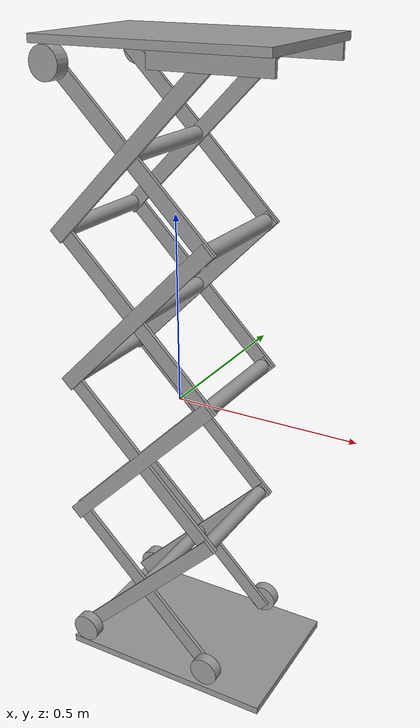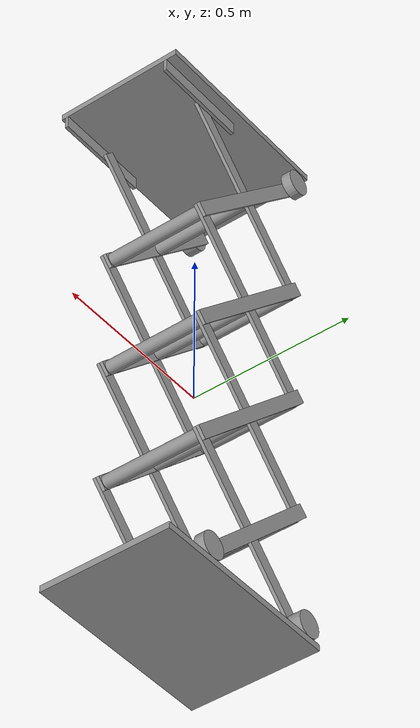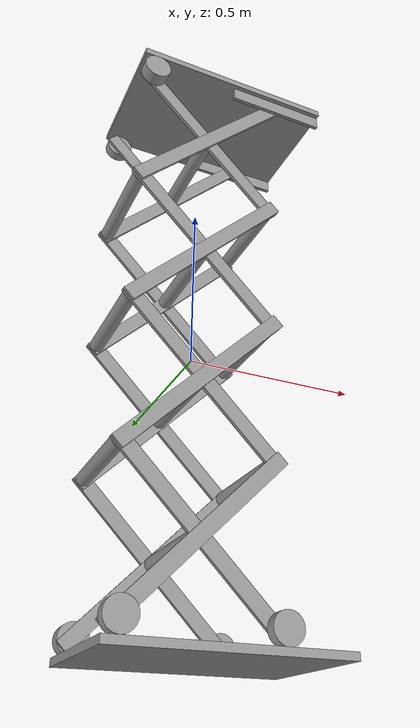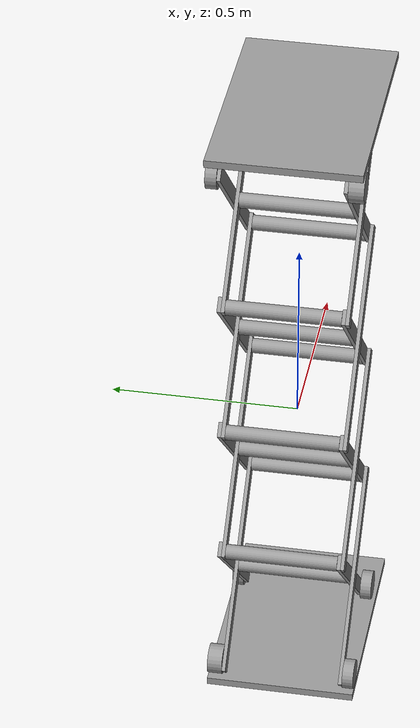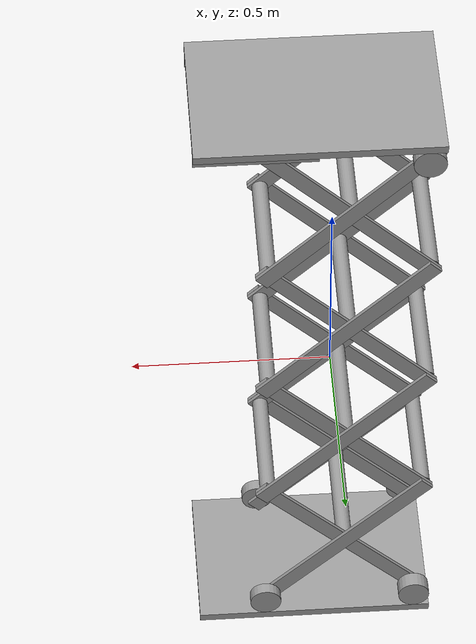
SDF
<?xml version='1.0'?>
<sdf version='1.6'>
  <model name='IMP3'>
    <link name='link_3'>
      <inertial>
        <mass>1</mass>
        <inertia>
          <ixx>0.166667</ixx>
          <ixy>0</ixy>
          <ixz>0</ixz>
          <iyy>0.166667</iyy>
          <iyz>0</iyz>
          <izz>0.166667</izz>
        </inertia>
        <pose frame=''>0 0 0 0 -0 0</pose>
      </inertial>
      <pose frame=''>0.047216 0.000242 -0.762232 0 -0 0</pose>
      <gravity>1</gravity>
      <self_collide>0</self_collide>
      <kinematic>0</kinematic>
      <enable_wind>0</enable_wind>
      <visual name='visual'>
        <pose frame=''>0 0 0 0 -0 0</pose>
        <geometry>
          <box>
            <size>0.6 0.4 0.02</size>
          </box>
        </geometry>
        <material>
          <lighting>1</lighting>
          <script>
            <uri>file://media/materials/scripts/gazebo.material</uri>
            <name>Gazebo/Grey</name>
          </script>
          <shader type='vertex'>
            <normal_map>__default__</normal_map>
          </shader>
          <ambient>0.3 0.3 0.3 1</ambient>
          <diffuse>0.7 0.7 0.7 1</diffuse>
          <specular>0.01 0.01 0.01 1</specular>
          <emissive>0 0 0 1</emissive>
        </material>
        <transparency>0</transparency>
        <cast_shadows>1</cast_shadows>
      </visual>
      <collision name='collision'>
        <laser_retro>0</laser_retro>
        <max_contacts>10</max_contacts>
        <pose frame=''>0 0 0 0 -0 0</pose>
        <geometry>
          <box>
            <size>0.6 0.4 0.02</size>
          </box>
        </geometry>
        <surface>
          <friction>
            <ode>
              <mu>1</mu>
              <mu2>1</mu2>
              <fdir1>0 0 0</fdir1>
              <slip1>0</slip1>
              <slip2>0</slip2>
            </ode>
            <torsional>
              <coefficient>1</coefficient>
              <patch_radius>0</patch_radius>
              <surface_radius>0</surface_radius>
              <use_patch_radius>1</use_patch_radius>
              <ode>
                <slip>0</slip>
              </ode>
            </torsional>
          </friction>
          <bounce>
            <restitution_coefficient>0</restitution_coefficient>
            <threshold>1e+06</threshold>
          </bounce>
          <contact>
            <collide_without_contact>0</collide_without_contact>
            <collide_without_contact_bitmask>1</collide_without_contact_bitmask>
            <collide_bitmask>1</collide_bitmask>
            <ode>
              <soft_cfm>0</soft_cfm>
              <soft_erp>0.2</soft_erp>
              <kp>1e+13</kp>
              <kd>1</kd>
              <max_vel>0.01</max_vel>
              <min_depth>0</min_depth>
            </ode>
            <bullet>
              <split_impulse>1</split_impulse>
              <split_impulse_penetration_threshold>-0.01</split_impulse_penetration_threshold>
              <soft_cfm>0</soft_cfm>
              <soft_erp>0.2</soft_erp>
              <kp>1e+13</kp>
              <kd>1</kd>
            </bullet>
          </contact>
        </surface>
      </collision>
    </link>
    <link name='link_3_clone'>
      <inertial>
        <mass>0.2</mass>
        <inertia>
          <ixx>0.00267333</ixx>
          <ixy>0</ixy>
          <ixz>0</ixz>
          <iyy>0.00600667</iyy>
          <iyz>0</iyz>
          <izz>0.00866667</izz>
        </inertia>
        <pose frame=''>0 0 0 0 -0 0</pose>
      </inertial>
      <pose frame=''>0.046736 0.002252 0.909368 0 -0 0</pose>
      <gravity>1</gravity>
      <self_collide>0</self_collide>
      <kinematic>0</kinematic>
      <enable_wind>0</enable_wind>
      <visual name='visual'>
        <pose frame=''>0 0 0 0 -0 0</pose>
        <geometry>
          <box>
            <size>0.6 0.4 0.02</size>
          </box>
        </geometry>
        <material>
          <lighting>1</lighting>
          <script>
            <uri>file://media/materials/scripts/gazebo.material</uri>
            <name>Gazebo/Grey</name>
          </script>
          <shader type='vertex'>
            <normal_map>__default__</normal_map>
          </shader>
          <ambient>0.3 0.3 0.3 1</ambient>
          <diffuse>0.7 0.7 0.7 1</diffuse>
          <specular>0.01 0.01 0.01 1</specular>
          <emissive>0 0 0 1</emissive>
        </material>
        <transparency>0</transparency>
        <cast_shadows>1</cast_shadows>
      </visual>
      <collision name='collision'>
        <laser_retro>0</laser_retro>
        <max_contacts>10</max_contacts>
        <pose frame=''>0 0 0 0 -0 0</pose>
        <geometry>
          <box>
            <size>0.6 0.4 0.02</size>
          </box>
        </geometry>
        <surface>
          <friction>
            <ode>
              <mu>1</mu>
              <mu2>1</mu2>
              <fdir1>0 0 0</fdir1>
              <slip1>0</slip1>
              <slip2>0</slip2>
            </ode>
            <torsional>
              <coefficient>1</coefficient>
              <patch_radius>0</patch_radius>
              <surface_radius>0</surface_radius>
              <use_patch_radius>1</use_patch_radius>
              <ode>
                <slip>0</slip>
              </ode>
            </torsional>
          </friction>
          <bounce>
            <restitution_coefficient>0</restitution_coefficient>
            <threshold>1e+06</threshold>
          </bounce>
          <contact>
            <collide_without_contact>0</collide_without_contact>
            <collide_without_contact_bitmask>1</collide_without_contact_bitmask>
            <collide_bitmask>1</collide_bitmask>
            <ode>
              <soft_cfm>0</soft_cfm>
              <soft_erp>0.2</soft_erp>
              <kp>1e+13</kp>
              <kd>1</kd>
              <max_vel>0.01</max_vel>
              <min_depth>0</min_depth>
            </ode>
            <bullet>
              <split_impulse>1</split_impulse>
              <split_impulse_penetration_threshold>-0.01</split_impulse_penetration_threshold>
              <soft_cfm>0</soft_cfm>
              <soft_erp>0.2</soft_erp>
              <kp>1e+13</kp>
              <kd>1</kd>
            </bullet>
          </contact>
        </surface>
      </collision>
    </link>
    <link name='link_4'>
      <inertial>
        <mass>1</mass>
        <inertia>
          <ixx>0.145833</ixx>
          <ixy>0</ixy>
          <ixz>0</ixz>
          <iyy>0.145833</iyy>
          <iyz>0</iyz>
          <izz>0.125</izz>
        </inertia>
        <pose frame=''>0 0 0 0 -0 0</pose>
      </inertial>
      <pose frame=''>-0.212784 -0.184758 -0.71223 1.5707 -0 0</pose>
      <gravity>1</gravity>
      <self_collide>0</self_collide>
      <kinematic>0</kinematic>
      <enable_wind>0</enable_wind>
      <visual name='visual'>
        <pose frame=''>0 0 0 0 -0 0</pose>
        <geometry>
          <cylinder>
            <radius>0.04</radius>
            <length>0.03</length>
          </cylinder>
        </geometry>
        <material>
          <lighting>1</lighting>
          <script>
            <uri>file://media/materials/scripts/gazebo.material</uri>
            <name>Gazebo/Grey</name>
          </script>
          <shader type='vertex'>
            <normal_map>__default__</normal_map>
          </shader>
          <ambient>0.3 0.3 0.3 1</ambient>
          <diffuse>0.7 0.7 0.7 1</diffuse>
          <specular>0.01 0.01 0.01 1</specular>
          <emissive>0 0 0 1</emissive>
        </material>
        <transparency>0</transparency>
        <cast_shadows>1</cast_shadows>
      </visual>
      <collision name='collision'>
        <laser_retro>0</laser_retro>
        <max_contacts>10</max_contacts>
        <pose frame=''>0 0 0 0 -0 0</pose>
        <geometry>
          <cylinder>
            <radius>0.04</radius>
            <length>0.03</length>
          </cylinder>
        </geometry>
        <surface>
          <friction>
            <ode>
              <mu>1</mu>
              <mu2>1</mu2>
              <fdir1>0 0 0</fdir1>
              <slip1>0</slip1>
              <slip2>0</slip2>
            </ode>
            <torsional>
              <coefficient>1</coefficient>
              <patch_radius>0</patch_radius>
              <surface_radius>0</surface_radius>
              <use_patch_radius>1</use_patch_radius>
              <ode>
                <slip>0</slip>
              </ode>
            </torsional>
          </friction>
          <bounce>
            <restitution_coefficient>0</restitution_coefficient>
            <threshold>1e+06</threshold>
          </bounce>
          <contact>
            <collide_without_contact>0</collide_without_contact>
            <collide_without_contact_bitmask>1</collide_without_contact_bitmask>
            <collide_bitmask>1</collide_bitmask>
            <ode>
              <soft_cfm>0</soft_cfm>
              <soft_erp>0.2</soft_erp>
              <kp>1e+13</kp>
              <kd>1</kd>
              <max_vel>0.01</max_vel>
              <min_depth>0</min_depth>
            </ode>
            <bullet>
              <split_impulse>1</split_impulse>
              <split_impulse_penetration_threshold>-0.01</split_impulse_penetration_threshold>
              <soft_cfm>0</soft_cfm>
              <soft_erp>0.2</soft_erp>
              <kp>1e+13</kp>
              <kd>1</kd>
            </bullet>
          </contact>
        </surface>
      </collision>
    </link>
    <link name='link_4_clone'>
      <inertial>
        <mass>1</mass>
        <inertia>
          <ixx>0.145833</ixx>
          <ixy>0</ixy>
          <ixz>0</ixz>
          <iyy>0.145833</iyy>
          <iyz>0</iyz>
          <izz>0.125</izz>
        </inertia>
        <pose frame=''>0 0 0 0 -0 0</pose>
      </inertial>
      <pose frame=''>-0.212784 0.180242 -0.712232 1.5707 -0 0</pose>
      <gravity>1</gravity>
      <self_collide>0</self_collide>
      <kinematic>0</kinematic>
      <enable_wind>0</enable_wind>
      <visual name='visual'>
        <pose frame=''>0 0 0 0 -0 0</pose>
        <geometry>
          <cylinder>
            <radius>0.04</radius>
            <length>0.04</length>
          </cylinder>
        </geometry>
        <material>
          <lighting>1</lighting>
          <script>
            <uri>file://media/materials/scripts/gazebo.material</uri>
            <name>Gazebo/Grey</name>
          </script>
          <shader type='vertex'>
            <normal_map>__default__</normal_map>
          </shader>
          <ambient>0.3 0.3 0.3 1</ambient>
          <diffuse>0.7 0.7 0.7 1</diffuse>
          <specular>0.01 0.01 0.01 1</specular>
          <emissive>0 0 0 1</emissive>
        </material>
        <transparency>0</transparency>
        <cast_shadows>1</cast_shadows>
      </visual>
      <collision name='collision'>
        <laser_retro>0</laser_retro>
        <max_contacts>10</max_contacts>
        <pose frame=''>0 0 0 0 -0 0</pose>
        <geometry>
          <cylinder>
            <radius>0.04</radius>
            <length>0.04</length>
          </cylinder>
        </geometry>
        <surface>
          <friction>
            <ode>
              <mu>1</mu>
              <mu2>1</mu2>
              <fdir1>0 0 0</fdir1>
              <slip1>0</slip1>
              <slip2>0</slip2>
            </ode>
            <torsional>
              <coefficient>1</coefficient>
              <patch_radius>0</patch_radius>
              <surface_radius>0</surface_radius>
              <use_patch_radius>1</use_patch_radius>
              <ode>
                <slip>0</slip>
              </ode>
            </torsional>
          </friction>
          <bounce>
            <restitution_coefficient>0</restitution_coefficient>
            <threshold>1e+06</threshold>
          </bounce>
          <contact>
            <collide_without_contact>0</collide_without_contact>
            <collide_without_contact_bitmask>1</collide_without_contact_bitmask>
            <collide_bitmask>1</collide_bitmask>
            <ode>
              <soft_cfm>0</soft_cfm>
              <soft_erp>0.2</soft_erp>
              <kp>1e+13</kp>
              <kd>1</kd>
              <max_vel>0.01</max_vel>
              <min_depth>0</min_depth>
            </ode>
            <bullet>
              <split_impulse>1</split_impulse>
              <split_impulse_penetration_threshold>-0.01</split_impulse_penetration_threshold>
              <soft_cfm>0</soft_cfm>
              <soft_erp>0.2</soft_erp>
              <kp>1e+13</kp>
              <kd>1</kd>
            </bullet>
          </contact>
        </surface>
      </collision>
    </link>
    <link name='link_4_clone_0'>
      <inertial>
        <mass>0.02</mass>
        <inertia>
          <ixx>1.067e-05</ixx>
          <ixy>0</ixy>
          <ixz>0</ixz>
          <iyy>1.067e-05</iyy>
          <iyz>0</iyz>
          <izz>1.6e-05</izz>
        </inertia>
        <pose frame=''>0 0 0 0 -0 0</pose>
      </inertial>
      <pose frame=''>-0.212813 -0.17977 0.858758 1.5707 -0 0</pose>
      <gravity>1</gravity>
      <self_collide>0</self_collide>
      <kinematic>0</kinematic>
      <enable_wind>0</enable_wind>
      <visual name='visual'>
        <pose frame=''>0 0 0 0 -0 0</pose>
        <geometry>
          <cylinder>
            <radius>0.04</radius>
            <length>0.04</length>
          </cylinder>
        </geometry>
        <material>
          <lighting>1</lighting>
          <script>
            <uri>file://media/materials/scripts/gazebo.material</uri>
            <name>Gazebo/Grey</name>
          </script>
          <shader type='vertex'>
            <normal_map>__default__</normal_map>
          </shader>
          <ambient>0.3 0.3 0.3 1</ambient>
          <diffuse>0.7 0.7 0.7 1</diffuse>
          <specular>0.01 0.01 0.01 1</specular>
          <emissive>0 0 0 1</emissive>
        </material>
        <transparency>0</transparency>
        <cast_shadows>1</cast_shadows>
      </visual>
      <collision name='collision'>
        <laser_retro>0</laser_retro>
        <max_contacts>10</max_contacts>
        <pose frame=''>0 0 0 0 -0 0</pose>
        <geometry>
          <cylinder>
            <radius>0.04</radius>
            <length>0.04</length>
          </cylinder>
        </geometry>
        <surface>
          <friction>
            <ode>
              <mu>1</mu>
              <mu2>1</mu2>
              <fdir1>0 0 0</fdir1>
              <slip1>0</slip1>
              <slip2>0</slip2>
            </ode>
            <torsional>
              <coefficient>1</coefficient>
              <patch_radius>0</patch_radius>
              <surface_radius>0</surface_radius>
              <use_patch_radius>1</use_patch_radius>
              <ode>
                <slip>0</slip>
              </ode>
            </torsional>
          </friction>
          <bounce>
            <restitution_coefficient>0</restitution_coefficient>
            <threshold>1e+06</threshold>
          </bounce>
          <contact>
            <collide_without_contact>0</collide_without_contact>
            <collide_without_contact_bitmask>1</collide_without_contact_bitmask>
            <collide_bitmask>1</collide_bitmask>
            <ode>
              <soft_cfm>0</soft_cfm>
              <soft_erp>0.2</soft_erp>
              <kp>1e+13</kp>
              <kd>1</kd>
              <max_vel>0.01</max_vel>
              <min_depth>0</min_depth>
            </ode>
            <bullet>
              <split_impulse>1</split_impulse>
              <split_impulse_penetration_threshold>-0.01</split_impulse_penetration_threshold>
              <soft_cfm>0</soft_cfm>
              <soft_erp>0.2</soft_erp>
              <kp>1e+13</kp>
              <kd>1</kd>
            </bullet>
          </contact>
        </surface>
      </collision>
    </link>
    <link name='link_4_clone_1'>
      <inertial>
        <mass>0.02</mass>
        <inertia>
          <ixx>9.5e-06</ixx>
          <ixy>0</ixy>
          <ixz>0</ixz>
          <iyy>9.5e-06</iyy>
          <iyz>0</iyz>
          <izz>1.6e-05</izz>
        </inertia>
        <pose frame=''>0 0 0 0 -0 0</pose>
      </inertial>
      <pose frame=''>-0.212784 0.185235 0.859238 1.5707 -0 0</pose>
      <gravity>1</gravity>
      <self_collide>0</self_collide>
      <kinematic>0</kinematic>
      <enable_wind>0</enable_wind>
      <visual name='visual'>
        <pose frame=''>0 0 0 0 -0 0</pose>
        <geometry>
          <cylinder>
            <radius>0.04</radius>
            <length>0.03</length>
          </cylinder>
        </geometry>
        <material>
          <lighting>1</lighting>
          <script>
            <uri>file://media/materials/scripts/gazebo.material</uri>
            <name>Gazebo/Grey</name>
          </script>
          <shader type='vertex'>
            <normal_map>__default__</normal_map>
          </shader>
          <ambient>0.3 0.3 0.3 1</ambient>
          <diffuse>0.7 0.7 0.7 1</diffuse>
          <specular>0.01 0.01 0.01 1</specular>
          <emissive>0 0 0 1</emissive>
        </material>
        <transparency>0</transparency>
        <cast_shadows>1</cast_shadows>
      </visual>
      <collision name='collision'>
        <laser_retro>0</laser_retro>
        <max_contacts>10</max_contacts>
        <pose frame=''>0 0 0 0 -0 0</pose>
        <geometry>
          <cylinder>
            <radius>0.04</radius>
            <length>0.03</length>
          </cylinder>
        </geometry>
        <surface>
          <friction>
            <ode>
              <mu>1</mu>
              <mu2>1</mu2>
              <fdir1>0 0 0</fdir1>
              <slip1>0</slip1>
              <slip2>0</slip2>
            </ode>
            <torsional>
              <coefficient>1</coefficient>
              <patch_radius>0</patch_radius>
              <surface_radius>0</surface_radius>
              <use_patch_radius>1</use_patch_radius>
              <ode>
                <slip>0</slip>
              </ode>
            </torsional>
          </friction>
          <bounce>
            <restitution_coefficient>0</restitution_coefficient>
            <threshold>1e+06</threshold>
          </bounce>
          <contact>
            <collide_without_contact>0</collide_without_contact>
            <collide_without_contact_bitmask>1</collide_without_contact_bitmask>
            <collide_bitmask>1</collide_bitmask>
            <ode>
              <soft_cfm>0</soft_cfm>
              <soft_erp>0.2</soft_erp>
              <kp>1e+13</kp>
              <kd>1</kd>
              <max_vel>0.01</max_vel>
              <min_depth>0</min_depth>
            </ode>
            <bullet>
              <split_impulse>1</split_impulse>
              <split_impulse_penetration_threshold>-0.01</split_impulse_penetration_threshold>
              <soft_cfm>0</soft_cfm>
              <soft_erp>0.2</soft_erp>
              <kp>1e+13</kp>
              <kd>1</kd>
            </bullet>
          </contact>
        </surface>
      </collision>
    </link>
    <link name='link_4_clone_2'>
      <inertial>
        <mass>1</mass>
        <inertia>
          <ixx>0.145833</ixx>
          <ixy>0</ixy>
          <ixz>0</ixz>
          <iyy>0.145833</iyy>
          <iyz>0</iyz>
          <izz>0.125</izz>
        </inertia>
        <pose frame=''>0 0 0 0 -0 0</pose>
      </inertial>
      <pose frame=''>0.175 -0.175 -0.712231 1.5707 -0 0</pose>
      <gravity>1</gravity>
      <self_collide>0</self_collide>
      <kinematic>0</kinematic>
      <enable_wind>0</enable_wind>
      <visual name='visual'>
        <pose frame=''>0 0 0 0 -0 0</pose>
        <geometry>
          <cylinder>
            <radius>0.04</radius>
            <length>0.03</length>
          </cylinder>
        </geometry>
        <material>
          <lighting>1</lighting>
          <script>
            <uri>file://media/materials/scripts/gazebo.material</uri>
            <name>Gazebo/Grey</name>
          </script>
          <shader type='vertex'>
            <normal_map>__default__</normal_map>
          </shader>
          <ambient>0.3 0.3 0.3 1</ambient>
          <diffuse>0.7 0.7 0.7 1</diffuse>
          <specular>0.01 0.01 0.01 1</specular>
          <emissive>0 0 0 1</emissive>
        </material>
        <transparency>0</transparency>
        <cast_shadows>1</cast_shadows>
      </visual>
      <collision name='collision'>
        <laser_retro>0</laser_retro>
        <max_contacts>10</max_contacts>
        <pose frame=''>0 0 0 0 -0 0</pose>
        <geometry>
          <cylinder>
            <radius>0.04</radius>
            <length>0.03</length>
          </cylinder>
        </geometry>
        <surface>
          <friction>
            <ode>
              <mu>1</mu>
              <mu2>1</mu2>
              <fdir1>0 0 0</fdir1>
              <slip1>0</slip1>
              <slip2>0</slip2>
            </ode>
            <torsional>
              <coefficient>1</coefficient>
              <patch_radius>0</patch_radius>
              <surface_radius>0</surface_radius>
              <use_patch_radius>1</use_patch_radius>
              <ode>
                <slip>0</slip>
              </ode>
            </torsional>
          </friction>
          <bounce>
            <restitution_coefficient>0</restitution_coefficient>
            <threshold>1e+06</threshold>
          </bounce>
          <contact>
            <collide_without_contact>0</collide_without_contact>
            <collide_without_contact_bitmask>1</collide_without_contact_bitmask>
            <collide_bitmask>1</collide_bitmask>
            <ode>
              <soft_cfm>0</soft_cfm>
              <soft_erp>0.2</soft_erp>
              <kp>1e+13</kp>
              <kd>1</kd>
              <max_vel>0.01</max_vel>
              <min_depth>0</min_depth>
            </ode>
            <bullet>
              <split_impulse>1</split_impulse>
              <split_impulse_penetration_threshold>-0.01</split_impulse_penetration_threshold>
              <soft_cfm>0</soft_cfm>
              <soft_erp>0.2</soft_erp>
              <kp>1e+13</kp>
              <kd>1</kd>
            </bullet>
          </contact>
        </surface>
      </collision>
    </link>
    <link name='link_4_clone_3'>
      <inertial>
        <mass>1</mass>
        <inertia>
          <ixx>0.145833</ixx>
          <ixy>0</ixy>
          <ixz>0</ixz>
          <iyy>0.145833</iyy>
          <iyz>0</iyz>
          <izz>0.125</izz>
        </inertia>
        <pose frame=''>0 0 0 0 -0 0</pose>
      </inertial>
      <pose frame=''>0.175 0.185 -0.71223 1.5707 -0 0</pose>
      <gravity>1</gravity>
      <self_collide>0</self_collide>
      <kinematic>0</kinematic>
      <enable_wind>0</enable_wind>
      <visual name='visual'>
        <pose frame=''>0 0 0 0 -0 0</pose>
        <geometry>
          <cylinder>
            <radius>0.04</radius>
            <length>0.03</length>
          </cylinder>
        </geometry>
        <material>
          <lighting>1</lighting>
          <script>
            <uri>file://media/materials/scripts/gazebo.material</uri>
            <name>Gazebo/Grey</name>
          </script>
          <shader type='vertex'>
            <normal_map>__default__</normal_map>
          </shader>
          <ambient>0.3 0.3 0.3 1</ambient>
          <diffuse>0.7 0.7 0.7 1</diffuse>
          <specular>0.01 0.01 0.01 1</specular>
          <emissive>0 0 0 1</emissive>
        </material>
        <transparency>0</transparency>
        <cast_shadows>1</cast_shadows>
      </visual>
      <collision name='collision'>
        <laser_retro>0</laser_retro>
        <max_contacts>10</max_contacts>
        <pose frame=''>0 0 0 0 -0 0</pose>
        <geometry>
          <cylinder>
            <radius>0.04</radius>
            <length>0.03</length>
          </cylinder>
        </geometry>
        <surface>
          <friction>
            <ode>
              <mu>1</mu>
              <mu2>1</mu2>
              <fdir1>0 0 0</fdir1>
              <slip1>0</slip1>
              <slip2>0</slip2>
            </ode>
            <torsional>
              <coefficient>1</coefficient>
              <patch_radius>0</patch_radius>
              <surface_radius>0</surface_radius>
              <use_patch_radius>1</use_patch_radius>
              <ode>
                <slip>0</slip>
              </ode>
            </torsional>
          </friction>
          <bounce>
            <restitution_coefficient>0</restitution_coefficient>
            <threshold>1e+06</threshold>
          </bounce>
          <contact>
            <collide_without_contact>0</collide_without_contact>
            <collide_without_contact_bitmask>1</collide_without_contact_bitmask>
            <collide_bitmask>1</collide_bitmask>
            <ode>
              <soft_cfm>0</soft_cfm>
              <soft_erp>0.2</soft_erp>
              <kp>1e+13</kp>
              <kd>1</kd>
              <max_vel>0.01</max_vel>
              <min_depth>0</min_depth>
            </ode>
            <bullet>
              <split_impulse>1</split_impulse>
              <split_impulse_penetration_threshold>-0.01</split_impulse_penetration_threshold>
              <soft_cfm>0</soft_cfm>
              <soft_erp>0.2</soft_erp>
              <kp>1e+13</kp>
              <kd>1</kd>
            </bullet>
          </contact>
        </surface>
      </collision>
    </link>
    <link name='link_5_clone_clone'>
      <inertial>
        <mass>0.02</mass>
        <inertia>
          <ixx>2.83e-06</ixx>
          <ixy>0</ixy>
          <ixz>0</ixz>
          <iyy>0.00015267</iyy>
          <iyz>0</iyz>
          <izz>0.00015017</izz>
        </inertia>
        <pose frame=''>0 0 0 0 -0 0</pose>
      </inertial>
      <pose frame=''>0.196736 -0.179758 0.879368 0 -0 0</pose>
      <gravity>1</gravity>
      <self_collide>0</self_collide>
      <kinematic>0</kinematic>
      <enable_wind>0</enable_wind>
      <visual name='visual'>
        <pose frame=''>0 0 0 0 -0 0</pose>
        <geometry>
          <box>
            <size>0.3 0.01 0.04</size>
          </box>
        </geometry>
        <material>
          <lighting>1</lighting>
          <script>
            <uri>file://media/materials/scripts/gazebo.material</uri>
            <name>Gazebo/Grey</name>
          </script>
          <shader type='vertex'>
            <normal_map>__default__</normal_map>
          </shader>
          <ambient>0.3 0.3 0.3 1</ambient>
          <diffuse>0.7 0.7 0.7 1</diffuse>
          <specular>0.01 0.01 0.01 1</specular>
          <emissive>0 0 0 1</emissive>
        </material>
        <transparency>0</transparency>
        <cast_shadows>1</cast_shadows>
      </visual>
      <collision name='collision'>
        <laser_retro>0</laser_retro>
        <max_contacts>10</max_contacts>
        <pose frame=''>0 0 0 0 -0 0</pose>
        <geometry>
          <box>
            <size>0.3 0.01 0.04</size>
          </box>
        </geometry>
        <surface>
          <friction>
            <ode>
              <mu>1</mu>
              <mu2>1</mu2>
              <fdir1>0 0 0</fdir1>
              <slip1>0</slip1>
              <slip2>0</slip2>
            </ode>
            <torsional>
              <coefficient>1</coefficient>
              <patch_radius>0</patch_radius>
              <surface_radius>0</surface_radius>
              <use_patch_radius>1</use_patch_radius>
              <ode>
                <slip>0</slip>
              </ode>
            </torsional>
          </friction>
          <bounce>
            <restitution_coefficient>0</restitution_coefficient>
            <threshold>1e+06</threshold>
          </bounce>
          <contact>
            <collide_without_contact>0</collide_without_contact>
            <collide_without_contact_bitmask>1</collide_without_contact_bitmask>
            <collide_bitmask>1</collide_bitmask>
            <ode>
              <soft_cfm>0</soft_cfm>
              <soft_erp>0.2</soft_erp>
              <kp>1e+13</kp>
              <kd>1</kd>
              <max_vel>0.01</max_vel>
              <min_depth>0</min_depth>
            </ode>
            <bullet>
              <split_impulse>1</split_impulse>
              <split_impulse_penetration_threshold>-0.01</split_impulse_penetration_threshold>
              <soft_cfm>0</soft_cfm>
              <soft_erp>0.2</soft_erp>
              <kp>1e+13</kp>
              <kd>1</kd>
            </bullet>
          </contact>
        </surface>
      </collision>
    </link>
    <link name='link_5_clone_clone_clone'>
      <inertial>
        <mass>0.02</mass>
        <inertia>
          <ixx>2.83e-06</ixx>
          <ixy>0</ixy>
          <ixz>0</ixz>
          <iyy>0.00015267</iyy>
          <iyz>0</iyz>
          <izz>0.00015017</izz>
        </inertia>
        <pose frame=''>0 0 0 0 -0 0</pose>
      </inertial>
      <pose frame=''>0.196736 0.165242 0.879368 0 -0 0</pose>
      <gravity>1</gravity>
      <self_collide>0</self_collide>
      <kinematic>0</kinematic>
      <enable_wind>0</enable_wind>
      <visual name='visual'>
        <pose frame=''>0 0 0 0 -0 0</pose>
        <geometry>
          <box>
            <size>0.3 0.01 0.04</size>
          </box>
        </geometry>
        <material>
          <lighting>1</lighting>
          <script>
            <uri>file://media/materials/scripts/gazebo.material</uri>
            <name>Gazebo/Grey</name>
          </script>
          <shader type='vertex'>
            <normal_map>__default__</normal_map>
          </shader>
          <ambient>0.3 0.3 0.3 1</ambient>
          <diffuse>0.7 0.7 0.7 1</diffuse>
          <specular>0.01 0.01 0.01 1</specular>
          <emissive>0 0 0 1</emissive>
        </material>
        <transparency>0</transparency>
        <cast_shadows>1</cast_shadows>
      </visual>
      <collision name='collision'>
        <laser_retro>0</laser_retro>
        <max_contacts>10</max_contacts>
        <pose frame=''>0 0 0 0 -0 0</pose>
        <geometry>
          <box>
            <size>0.3 0.01 0.04</size>
          </box>
        </geometry>
        <surface>
          <friction>
            <ode>
              <mu>1</mu>
              <mu2>1</mu2>
              <fdir1>0 0 0</fdir1>
              <slip1>0</slip1>
              <slip2>0</slip2>
            </ode>
            <torsional>
              <coefficient>1</coefficient>
              <patch_radius>0</patch_radius>
              <surface_radius>0</surface_radius>
              <use_patch_radius>1</use_patch_radius>
              <ode>
                <slip>0</slip>
              </ode>
            </torsional>
          </friction>
          <bounce>
            <restitution_coefficient>0</restitution_coefficient>
            <threshold>1e+06</threshold>
          </bounce>
          <contact>
            <collide_without_contact>0</collide_without_contact>
            <collide_without_contact_bitmask>1</collide_without_contact_bitmask>
            <collide_bitmask>1</collide_bitmask>
            <ode>
              <soft_cfm>0</soft_cfm>
              <soft_erp>0.2</soft_erp>
              <kp>1e+13</kp>
              <kd>1</kd>
              <max_vel>0.01</max_vel>
              <min_depth>0</min_depth>
            </ode>
            <bullet>
              <split_impulse>1</split_impulse>
              <split_impulse_penetration_threshold>-0.01</split_impulse_penetration_threshold>
              <soft_cfm>0</soft_cfm>
              <soft_erp>0.2</soft_erp>
              <kp>1e+13</kp>
              <kd>1</kd>
            </bullet>
          </contact>
        </surface>
      </collision>
    </link>
    <model name='finaljointscissormodel'>
      <link name='link_2'>
        <inertial>
          <mass>1</mass>
          <inertia>
            <ixx>0.145833</ixx>
            <ixy>0</ixy>
            <ixz>0</ixz>
            <iyy>0.145833</iyy>
            <iyz>0</iyz>
            <izz>0.125</izz>
          </inertia>
          <pose frame=''>0 0 0 0 -0 0</pose>
        </inertial>
        <pose frame=''>-0 -0 0.212132 1.5707 -0 0</pose>
        <gravity>1</gravity>
        <self_collide>0</self_collide>
        <kinematic>0</kinematic>
        <enable_wind>0</enable_wind>
        <visual name='visual'>
          <pose frame=''>0 0 0 0 -0 0</pose>
          <geometry>
            <cylinder>
              <radius>0.02</radius>
              <length>0.3</length>
            </cylinder>
          </geometry>
          <material>
            <lighting>1</lighting>
            <script>
              <uri>file://media/materials/scripts/gazebo.material</uri>
              <name>Gazebo/Grey</name>
            </script>
            <shader type='vertex'>
              <normal_map>__default__</normal_map>
            </shader>
            <ambient>0.3 0.3 0.3 1</ambient>
            <diffuse>0.7 0.7 0.7 1</diffuse>
            <specular>0.01 0.01 0.01 1</specular>
            <emissive>0 0 0 1</emissive>
          </material>
          <transparency>0</transparency>
          <cast_shadows>1</cast_shadows>
        </visual>
        <collision name='collision'>
          <laser_retro>0</laser_retro>
          <max_contacts>10</max_contacts>
          <pose frame=''>0 0 0 0 -0 0</pose>
          <geometry>
            <cylinder>
              <radius>0.02</radius>
              <length>0.3</length>
            </cylinder>
          </geometry>
          <surface>
            <friction>
              <ode>
                <mu>1</mu>
                <mu2>1</mu2>
                <fdir1>0 0 0</fdir1>
                <slip1>0</slip1>
                <slip2>0</slip2>
              </ode>
              <torsional>
                <coefficient>1</coefficient>
                <patch_radius>0</patch_radius>
                <surface_radius>0</surface_radius>
                <use_patch_radius>1</use_patch_radius>
                <ode>
                  <slip>0</slip>
                </ode>
              </torsional>
            </friction>
            <bounce>
              <restitution_coefficient>0</restitution_coefficient>
              <threshold>1e+06</threshold>
            </bounce>
            <contact>
              <collide_without_contact>0</collide_without_contact>
              <collide_without_contact_bitmask>1</collide_without_contact_bitmask>
              <collide_bitmask>1</collide_bitmask>
              <ode>
                <soft_cfm>0</soft_cfm>
                <soft_erp>0.2</soft_erp>
                <kp>1e+13</kp>
                <kd>1</kd>
                <max_vel>0.01</max_vel>
                <min_depth>0</min_depth>
              </ode>
              <bullet>
                <split_impulse>1</split_impulse>
                <split_impulse_penetration_threshold>-0.01</split_impulse_penetration_threshold>
                <soft_cfm>0</soft_cfm>
                <soft_erp>0.2</soft_erp>
                <kp>1e+13</kp>
                <kd>1</kd>
              </bullet>
            </contact>
          </surface>
        </collision>
      </link>
      <link name='link_2_clone'>
        <inertial>
          <mass>1</mass>
          <inertia>
            <ixx>0.145833</ixx>
            <ixy>0</ixy>
            <ixz>0</ixz>
            <iyy>0.145833</iyy>
            <iyz>0</iyz>
            <izz>0.125</izz>
          </inertia>
          <pose frame=''>0 0 0 0 -0 0</pose>
        </inertial>
        <pose frame=''>-0 -0 0.608111 1.5707 -0 0</pose>
        <gravity>1</gravity>
        <self_collide>0</self_collide>
        <kinematic>0</kinematic>
        <enable_wind>0</enable_wind>
        <visual name='visual'>
          <pose frame=''>0 0 0 0 -0 0</pose>
          <geometry>
            <cylinder>
              <radius>0.02</radius>
              <length>0.3</length>
            </cylinder>
          </geometry>
          <material>
            <lighting>1</lighting>
            <script>
              <uri>file://media/materials/scripts/gazebo.material</uri>
              <name>Gazebo/Grey</name>
            </script>
            <shader type='vertex'>
              <normal_map>__default__</normal_map>
            </shader>
            <ambient>0.3 0.3 0.3 1</ambient>
            <diffuse>0.7 0.7 0.7 1</diffuse>
            <specular>0.01 0.01 0.01 1</specular>
            <emissive>0 0 0 1</emissive>
          </material>
          <transparency>0</transparency>
          <cast_shadows>1</cast_shadows>
        </visual>
        <collision name='collision'>
          <laser_retro>0</laser_retro>
          <max_contacts>10</max_contacts>
          <pose frame=''>0 0 0 0 -0 0</pose>
          <geometry>
            <cylinder>
              <radius>0.02</radius>
              <length>0.3</length>
            </cylinder>
          </geometry>
          <surface>
            <friction>
              <ode>
                <mu>1</mu>
                <mu2>1</mu2>
                <fdir1>0 0 0</fdir1>
                <slip1>0</slip1>
                <slip2>0</slip2>
              </ode>
              <torsional>
                <coefficient>1</coefficient>
                <patch_radius>0</patch_radius>
                <surface_radius>0</surface_radius>
                <use_patch_radius>1</use_patch_radius>
                <ode>
                  <slip>0</slip>
                </ode>
              </torsional>
            </friction>
            <bounce>
              <restitution_coefficient>0</restitution_coefficient>
              <threshold>1e+06</threshold>
            </bounce>
            <contact>
              <collide_without_contact>0</collide_without_contact>
              <collide_without_contact_bitmask>1</collide_without_contact_bitmask>
              <collide_bitmask>1</collide_bitmask>
              <ode>
                <soft_cfm>0</soft_cfm>
                <soft_erp>0.2</soft_erp>
                <kp>1e+13</kp>
                <kd>1</kd>
                <max_vel>0.01</max_vel>
                <min_depth>0</min_depth>
              </ode>
              <bullet>
                <split_impulse>1</split_impulse>
                <split_impulse_penetration_threshold>-0.01</split_impulse_penetration_threshold>
                <soft_cfm>0</soft_cfm>
                <soft_erp>0.2</soft_erp>
                <kp>1e+13</kp>
                <kd>1</kd>
              </bullet>
            </contact>
          </surface>
        </collision>
      </link>
      <link name='link_2_clone_0'>
        <inertial>
          <mass>1</mass>
          <inertia>
            <ixx>0.145833</ixx>
            <ixy>0</ixy>
            <ixz>0</ixz>
            <iyy>0.145833</iyy>
            <iyz>0</iyz>
            <izz>0.125</izz>
          </inertia>
          <pose frame=''>0 0 0 0 -0 0</pose>
        </inertial>
        <pose frame=''>-0 -0 1.00409 1.5707 -0 0</pose>
        <gravity>1</gravity>
        <self_collide>0</self_collide>
        <kinematic>0</kinematic>
        <enable_wind>0</enable_wind>
        <visual name='visual'>
          <pose frame=''>0 0 0 0 -0 0</pose>
          <geometry>
            <cylinder>
              <radius>0.02</radius>
              <length>0.3</length>
            </cylinder>
          </geometry>
          <material>
            <lighting>1</lighting>
            <script>
              <uri>file://media/materials/scripts/gazebo.material</uri>
              <name>Gazebo/Grey</name>
            </script>
            <shader type='vertex'>
              <normal_map>__default__</normal_map>
            </shader>
            <ambient>0.3 0.3 0.3 1</ambient>
            <diffuse>0.7 0.7 0.7 1</diffuse>
            <specular>0.01 0.01 0.01 1</specular>
            <emissive>0 0 0 1</emissive>
          </material>
          <transparency>0</transparency>
          <cast_shadows>1</cast_shadows>
        </visual>
        <collision name='collision'>
          <laser_retro>0</laser_retro>
          <max_contacts>10</max_contacts>
          <pose frame=''>0 0 0 0 -0 0</pose>
          <geometry>
            <cylinder>
              <radius>0.02</radius>
              <length>0.3</length>
            </cylinder>
          </geometry>
          <surface>
            <friction>
              <ode>
                <mu>1</mu>
                <mu2>1</mu2>
                <fdir1>0 0 0</fdir1>
                <slip1>0</slip1>
                <slip2>0</slip2>
              </ode>
              <torsional>
                <coefficient>1</coefficient>
                <patch_radius>0</patch_radius>
                <surface_radius>0</surface_radius>
                <use_patch_radius>1</use_patch_radius>
                <ode>
                  <slip>0</slip>
                </ode>
              </torsional>
            </friction>
            <bounce>
              <restitution_coefficient>0</restitution_coefficient>
              <threshold>1e+06</threshold>
            </bounce>
            <contact>
              <collide_without_contact>0</collide_without_contact>
              <collide_without_contact_bitmask>1</collide_without_contact_bitmask>
              <collide_bitmask>1</collide_bitmask>
              <ode>
                <soft_cfm>0</soft_cfm>
                <soft_erp>0.2</soft_erp>
                <kp>1e+13</kp>
                <kd>1</kd>
                <max_vel>0.01</max_vel>
                <min_depth>0</min_depth>
              </ode>
              <bullet>
                <split_impulse>1</split_impulse>
                <split_impulse_penetration_threshold>-0.01</split_impulse_penetration_threshold>
                <soft_cfm>0</soft_cfm>
                <soft_erp>0.2</soft_erp>
                <kp>1e+13</kp>
                <kd>1</kd>
              </bullet>
            </contact>
          </surface>
        </collision>
      </link>
      <link name='link_2_clone_0_clone'>
        <inertial>
          <mass>1</mass>
          <inertia>
            <ixx>0.145833</ixx>
            <ixy>0</ixy>
            <ixz>0</ixz>
            <iyy>0.145833</iyy>
            <iyz>0</iyz>
            <izz>0.125</izz>
          </inertia>
          <pose frame=''>0 0 0 0 -0 0</pose>
        </inertial>
        <pose frame=''>-0 -0 1.40007 1.5707 -0 0</pose>
        <gravity>1</gravity>
        <self_collide>0</self_collide>
        <kinematic>0</kinematic>
        <enable_wind>0</enable_wind>
        <visual name='visual'>
          <pose frame=''>0 0 0 0 -0 0</pose>
          <geometry>
            <cylinder>
              <radius>0.02</radius>
              <length>0.3</length>
            </cylinder>
          </geometry>
          <material>
            <lighting>1</lighting>
            <script>
              <uri>file://media/materials/scripts/gazebo.material</uri>
              <name>Gazebo/Grey</name>
            </script>
            <shader type='vertex'>
              <normal_map>__default__</normal_map>
            </shader>
            <ambient>0.3 0.3 0.3 1</ambient>
            <diffuse>0.7 0.7 0.7 1</diffuse>
            <specular>0.01 0.01 0.01 1</specular>
            <emissive>0 0 0 1</emissive>
          </material>
          <transparency>0</transparency>
          <cast_shadows>1</cast_shadows>
        </visual>
        <collision name='collision'>
          <laser_retro>0</laser_retro>
          <max_contacts>10</max_contacts>
          <pose frame=''>0 0 0 0 -0 0</pose>
          <geometry>
            <cylinder>
              <radius>0.02</radius>
              <length>0.3</length>
            </cylinder>
          </geometry>
          <surface>
            <friction>
              <ode>
                <mu>1</mu>
                <mu2>1</mu2>
                <fdir1>0 0 0</fdir1>
                <slip1>0</slip1>
                <slip2>0</slip2>
              </ode>
              <torsional>
                <coefficient>1</coefficient>
                <patch_radius>0</patch_radius>
                <surface_radius>0</surface_radius>
                <use_patch_radius>1</use_patch_radius>
                <ode>
                  <slip>0</slip>
                </ode>
              </torsional>
            </friction>
            <bounce>
              <restitution_coefficient>0</restitution_coefficient>
              <threshold>1e+06</threshold>
            </bounce>
            <contact>
              <collide_without_contact>0</collide_without_contact>
              <collide_without_contact_bitmask>1</collide_without_contact_bitmask>
              <collide_bitmask>1</collide_bitmask>
              <ode>
                <soft_cfm>0</soft_cfm>
                <soft_erp>0.2</soft_erp>
                <kp>1e+13</kp>
                <kd>1</kd>
                <max_vel>0.01</max_vel>
                <min_depth>0</min_depth>
              </ode>
              <bullet>
                <split_impulse>1</split_impulse>
                <split_impulse_penetration_threshold>-0.01</split_impulse_penetration_threshold>
                <soft_cfm>0</soft_cfm>
                <soft_erp>0.2</soft_erp>
                <kp>1e+13</kp>
                <kd>1</kd>
              </bullet>
            </contact>
          </surface>
        </collision>
      </link>
      <link name='link_2_clone_0_clone_0'>
        <inertial>
          <mass>1</mass>
          <inertia>
            <ixx>0.145833</ixx>
            <ixy>0</ixy>
            <ixz>0</ixz>
            <iyy>0.145833</iyy>
            <iyz>0</iyz>
            <izz>0.125</izz>
          </inertia>
          <pose frame=''>0 0 0 0 -0 0</pose>
        </inertial>
        <pose frame=''>0.197989 -0 0.410121 1.5707 -0 0</pose>
        <gravity>1</gravity>
        <self_collide>0</self_collide>
        <kinematic>0</kinematic>
        <enable_wind>0</enable_wind>
        <visual name='visual'>
          <pose frame=''>0 0 0 0 -0 0</pose>
          <geometry>
            <cylinder>
              <radius>0.02</radius>
              <length>0.3</length>
            </cylinder>
          </geometry>
          <material>
            <lighting>1</lighting>
            <script>
              <uri>file://media/materials/scripts/gazebo.material</uri>
              <name>Gazebo/Grey</name>
            </script>
            <shader type='vertex'>
              <normal_map>__default__</normal_map>
            </shader>
            <ambient>0.3 0.3 0.3 1</ambient>
            <diffuse>0.7 0.7 0.7 1</diffuse>
            <specular>0.01 0.01 0.01 1</specular>
            <emissive>0 0 0 1</emissive>
          </material>
          <transparency>0</transparency>
          <cast_shadows>1</cast_shadows>
        </visual>
        <collision name='collision'>
          <laser_retro>0</laser_retro>
          <max_contacts>10</max_contacts>
          <pose frame=''>0 0 0 0 -0 0</pose>
          <geometry>
            <cylinder>
              <radius>0.02</radius>
              <length>0.3</length>
            </cylinder>
          </geometry>
          <surface>
            <friction>
              <ode>
                <mu>1</mu>
                <mu2>1</mu2>
                <fdir1>0 0 0</fdir1>
                <slip1>0</slip1>
                <slip2>0</slip2>
              </ode>
              <torsional>
                <coefficient>1</coefficient>
                <patch_radius>0</patch_radius>
                <surface_radius>0</surface_radius>
                <use_patch_radius>1</use_patch_radius>
                <ode>
                  <slip>0</slip>
                </ode>
              </torsional>
            </friction>
            <bounce>
              <restitution_coefficient>0</restitution_coefficient>
              <threshold>1e+06</threshold>
            </bounce>
            <contact>
              <collide_without_contact>0</collide_without_contact>
              <collide_without_contact_bitmask>1</collide_without_contact_bitmask>
              <collide_bitmask>1</collide_bitmask>
              <ode>
                <soft_cfm>0</soft_cfm>
                <soft_erp>0.2</soft_erp>
                <kp>1e+13</kp>
                <kd>1</kd>
                <max_vel>0.01</max_vel>
                <min_depth>0</min_depth>
              </ode>
              <bullet>
                <split_impulse>1</split_impulse>
                <split_impulse_penetration_threshold>-0.01</split_impulse_penetration_threshold>
                <soft_cfm>0</soft_cfm>
                <soft_erp>0.2</soft_erp>
                <kp>1e+13</kp>
                <kd>1</kd>
              </bullet>
            </contact>
          </surface>
        </collision>
      </link>
      <link name='link_2_clone_0_clone_1'>
        <inertial>
          <mass>1</mass>
          <inertia>
            <ixx>0.145833</ixx>
            <ixy>0</ixy>
            <ixz>0</ixz>
            <iyy>0.145833</iyy>
            <iyz>0</iyz>
            <izz>0.125</izz>
          </inertia>
          <pose frame=''>0 0 0 0 -0 0</pose>
        </inertial>
        <pose frame=''>-0.197989 -0 0.410121 1.5707 -0 0</pose>
        <gravity>1</gravity>
        <self_collide>0</self_collide>
        <kinematic>0</kinematic>
        <enable_wind>0</enable_wind>
        <visual name='visual'>
          <pose frame=''>0 0 0 0 -0 0</pose>
          <geometry>
            <cylinder>
              <radius>0.02</radius>
              <length>0.3</length>
            </cylinder>
          </geometry>
          <material>
            <lighting>1</lighting>
            <script>
              <uri>file://media/materials/scripts/gazebo.material</uri>
              <name>Gazebo/Grey</name>
            </script>
            <shader type='vertex'>
              <normal_map>__default__</normal_map>
            </shader>
            <ambient>0.3 0.3 0.3 1</ambient>
            <diffuse>0.7 0.7 0.7 1</diffuse>
            <specular>0.01 0.01 0.01 1</specular>
            <emissive>0 0 0 1</emissive>
          </material>
          <transparency>0</transparency>
          <cast_shadows>1</cast_shadows>
        </visual>
        <collision name='collision'>
          <laser_retro>0</laser_retro>
          <max_contacts>10</max_contacts>
          <pose frame=''>0 0 0 0 -0 0</pose>
          <geometry>
            <cylinder>
              <radius>0.02</radius>
              <length>0.3</length>
            </cylinder>
          </geometry>
          <surface>
            <friction>
              <ode>
                <mu>1</mu>
                <mu2>1</mu2>
                <fdir1>0 0 0</fdir1>
                <slip1>0</slip1>
                <slip2>0</slip2>
              </ode>
              <torsional>
                <coefficient>1</coefficient>
                <patch_radius>0</patch_radius>
                <surface_radius>0</surface_radius>
                <use_patch_radius>1</use_patch_radius>
                <ode>
                  <slip>0</slip>
                </ode>
              </torsional>
            </friction>
            <bounce>
              <restitution_coefficient>0</restitution_coefficient>
              <threshold>1e+06</threshold>
            </bounce>
            <contact>
              <collide_without_contact>0</collide_without_contact>
              <collide_without_contact_bitmask>1</collide_without_contact_bitmask>
              <collide_bitmask>1</collide_bitmask>
              <ode>
                <soft_cfm>0</soft_cfm>
                <soft_erp>0.2</soft_erp>
                <kp>1e+13</kp>
                <kd>1</kd>
                <max_vel>0.01</max_vel>
                <min_depth>0</min_depth>
              </ode>
              <bullet>
                <split_impulse>1</split_impulse>
                <split_impulse_penetration_threshold>-0.01</split_impulse_penetration_threshold>
                <soft_cfm>0</soft_cfm>
                <soft_erp>0.2</soft_erp>
                <kp>1e+13</kp>
                <kd>1</kd>
              </bullet>
            </contact>
          </surface>
        </collision>
      </link>
      <link name='link_2_clone_0_clone_2'>
        <inertial>
          <mass>1</mass>
          <inertia>
            <ixx>0.145833</ixx>
            <ixy>0</ixy>
            <ixz>0</ixz>
            <iyy>0.145833</iyy>
            <iyz>0</iyz>
            <izz>0.125</izz>
          </inertia>
          <pose frame=''>0 0 0 0 -0 0</pose>
        </inertial>
        <pose frame=''>0.197989 -0 1.20208 1.5707 -0 0</pose>
        <gravity>1</gravity>
        <self_collide>0</self_collide>
        <kinematic>0</kinematic>
        <enable_wind>0</enable_wind>
        <visual name='visual'>
          <pose frame=''>0 0 0 0 -0 0</pose>
          <geometry>
            <cylinder>
              <radius>0.02</radius>
              <length>0.3</length>
            </cylinder>
          </geometry>
          <material>
            <lighting>1</lighting>
            <script>
              <uri>file://media/materials/scripts/gazebo.material</uri>
              <name>Gazebo/Grey</name>
            </script>
            <shader type='vertex'>
              <normal_map>__default__</normal_map>
            </shader>
            <ambient>0.3 0.3 0.3 1</ambient>
            <diffuse>0.7 0.7 0.7 1</diffuse>
            <specular>0.01 0.01 0.01 1</specular>
            <emissive>0 0 0 1</emissive>
          </material>
          <transparency>0</transparency>
          <cast_shadows>1</cast_shadows>
        </visual>
        <collision name='collision'>
          <laser_retro>0</laser_retro>
          <max_contacts>10</max_contacts>
          <pose frame=''>0 0 0 0 -0 0</pose>
          <geometry>
            <cylinder>
              <radius>0.02</radius>
              <length>0.3</length>
            </cylinder>
          </geometry>
          <surface>
            <friction>
              <ode>
                <mu>1</mu>
                <mu2>1</mu2>
                <fdir1>0 0 0</fdir1>
                <slip1>0</slip1>
                <slip2>0</slip2>
              </ode>
              <torsional>
                <coefficient>1</coefficient>
                <patch_radius>0</patch_radius>
                <surface_radius>0</surface_radius>
                <use_patch_radius>1</use_patch_radius>
                <ode>
                  <slip>0</slip>
                </ode>
              </torsional>
            </friction>
            <bounce>
              <restitution_coefficient>0</restitution_coefficient>
              <threshold>1e+06</threshold>
            </bounce>
            <contact>
              <collide_without_contact>0</collide_without_contact>
              <collide_without_contact_bitmask>1</collide_without_contact_bitmask>
              <collide_bitmask>1</collide_bitmask>
              <ode>
                <soft_cfm>0</soft_cfm>
                <soft_erp>0.2</soft_erp>
                <kp>1e+13</kp>
                <kd>1</kd>
                <max_vel>0.01</max_vel>
                <min_depth>0</min_depth>
              </ode>
              <bullet>
                <split_impulse>1</split_impulse>
                <split_impulse_penetration_threshold>-0.01</split_impulse_penetration_threshold>
                <soft_cfm>0</soft_cfm>
                <soft_erp>0.2</soft_erp>
                <kp>1e+13</kp>
                <kd>1</kd>
              </bullet>
            </contact>
          </surface>
        </collision>
      </link>
      <link name='link_2_clone_0_clone_3'>
        <inertial>
          <mass>1</mass>
          <inertia>
            <ixx>0.145833</ixx>
            <ixy>0</ixy>
            <ixz>0</ixz>
            <iyy>0.145833</iyy>
            <iyz>0</iyz>
            <izz>0.125</izz>
          </inertia>
          <pose frame=''>0 0 0 0 -0 0</pose>
        </inertial>
        <pose frame=''>0.197989 -0 0.806101 1.5707 -0 0</pose>
        <gravity>1</gravity>
        <self_collide>0</self_collide>
        <kinematic>0</kinematic>
        <enable_wind>0</enable_wind>
        <visual name='visual'>
          <pose frame=''>0 0 0 0 -0 0</pose>
          <geometry>
            <cylinder>
              <radius>0.02</radius>
              <length>0.3</length>
            </cylinder>
          </geometry>
          <material>
            <lighting>1</lighting>
            <script>
              <uri>file://media/materials/scripts/gazebo.material</uri>
              <name>Gazebo/Grey</name>
            </script>
            <shader type='vertex'>
              <normal_map>__default__</normal_map>
            </shader>
            <ambient>0.3 0.3 0.3 1</ambient>
            <diffuse>0.7 0.7 0.7 1</diffuse>
            <specular>0.01 0.01 0.01 1</specular>
            <emissive>0 0 0 1</emissive>
          </material>
          <transparency>0</transparency>
          <cast_shadows>1</cast_shadows>
        </visual>
        <collision name='collision'>
          <laser_retro>0</laser_retro>
          <max_contacts>10</max_contacts>
          <pose frame=''>0 0 0 0 -0 0</pose>
          <geometry>
            <cylinder>
              <radius>0.02</radius>
              <length>0.3</length>
            </cylinder>
          </geometry>
          <surface>
            <friction>
              <ode>
                <mu>1</mu>
                <mu2>1</mu2>
                <fdir1>0 0 0</fdir1>
                <slip1>0</slip1>
                <slip2>0</slip2>
              </ode>
              <torsional>
                <coefficient>1</coefficient>
                <patch_radius>0</patch_radius>
                <surface_radius>0</surface_radius>
                <use_patch_radius>1</use_patch_radius>
                <ode>
                  <slip>0</slip>
                </ode>
              </torsional>
            </friction>
            <bounce>
              <restitution_coefficient>0</restitution_coefficient>
              <threshold>1e+06</threshold>
            </bounce>
            <contact>
              <collide_without_contact>0</collide_without_contact>
              <collide_without_contact_bitmask>1</collide_without_contact_bitmask>
              <collide_bitmask>1</collide_bitmask>
              <ode>
                <soft_cfm>0</soft_cfm>
                <soft_erp>0.2</soft_erp>
                <kp>1e+13</kp>
                <kd>1</kd>
                <max_vel>0.01</max_vel>
                <min_depth>0</min_depth>
              </ode>
              <bullet>
                <split_impulse>1</split_impulse>
                <split_impulse_penetration_threshold>-0.01</split_impulse_penetration_threshold>
                <soft_cfm>0</soft_cfm>
                <soft_erp>0.2</soft_erp>
                <kp>1e+13</kp>
                <kd>1</kd>
              </bullet>
            </contact>
          </surface>
        </collision>
      </link>
      <link name='link_2_clone_0_clone_4'>
        <inertial>
          <mass>1</mass>
          <inertia>
            <ixx>0.145833</ixx>
            <ixy>0</ixy>
            <ixz>0</ixz>
            <iyy>0.145833</iyy>
            <iyz>0</iyz>
            <izz>0.125</izz>
          </inertia>
          <pose frame=''>0 0 0 0 -0 0</pose>
        </inertial>
        <pose frame=''>-0.197989 -0 0.806101 1.5707 -0 0</pose>
        <gravity>1</gravity>
        <self_collide>0</self_collide>
        <kinematic>0</kinematic>
        <enable_wind>0</enable_wind>
        <visual name='visual'>
          <pose frame=''>0 0 0 0 -0 0</pose>
          <geometry>
            <cylinder>
              <radius>0.02</radius>
              <length>0.3</length>
            </cylinder>
          </geometry>
          <material>
            <lighting>1</lighting>
            <script>
              <uri>file://media/materials/scripts/gazebo.material</uri>
              <name>Gazebo/Grey</name>
            </script>
            <shader type='vertex'>
              <normal_map>__default__</normal_map>
            </shader>
            <ambient>0.3 0.3 0.3 1</ambient>
            <diffuse>0.7 0.7 0.7 1</diffuse>
            <specular>0.01 0.01 0.01 1</specular>
            <emissive>0 0 0 1</emissive>
          </material>
          <transparency>0</transparency>
          <cast_shadows>1</cast_shadows>
        </visual>
        <collision name='collision'>
          <laser_retro>0</laser_retro>
          <max_contacts>10</max_contacts>
          <pose frame=''>0 0 0 0 -0 0</pose>
          <geometry>
            <cylinder>
              <radius>0.02</radius>
              <length>0.3</length>
            </cylinder>
          </geometry>
          <surface>
            <friction>
              <ode>
                <mu>1</mu>
                <mu2>1</mu2>
                <fdir1>0 0 0</fdir1>
                <slip1>0</slip1>
                <slip2>0</slip2>
              </ode>
              <torsional>
                <coefficient>1</coefficient>
                <patch_radius>0</patch_radius>
                <surface_radius>0</surface_radius>
                <use_patch_radius>1</use_patch_radius>
                <ode>
                  <slip>0</slip>
                </ode>
              </torsional>
            </friction>
            <bounce>
              <restitution_coefficient>0</restitution_coefficient>
              <threshold>1e+06</threshold>
            </bounce>
            <contact>
              <collide_without_contact>0</collide_without_contact>
              <collide_without_contact_bitmask>1</collide_without_contact_bitmask>
              <collide_bitmask>1</collide_bitmask>
              <ode>
                <soft_cfm>0</soft_cfm>
                <soft_erp>0.2</soft_erp>
                <kp>1e+13</kp>
                <kd>1</kd>
                <max_vel>0.01</max_vel>
                <min_depth>0</min_depth>
              </ode>
              <bullet>
                <split_impulse>1</split_impulse>
                <split_impulse_penetration_threshold>-0.01</split_impulse_penetration_threshold>
                <soft_cfm>0</soft_cfm>
                <soft_erp>0.2</soft_erp>
                <kp>1e+13</kp>
                <kd>1</kd>
              </bullet>
            </contact>
          </surface>
        </collision>
      </link>
      <link name='link_2_clone_0_clone_5'>
        <inertial>
          <mass>1</mass>
          <inertia>
            <ixx>0.145833</ixx>
            <ixy>0</ixy>
            <ixz>0</ixz>
            <iyy>0.145833</iyy>
            <iyz>0</iyz>
            <izz>0.125</izz>
          </inertia>
          <pose frame=''>0 0 0 0 -0 0</pose>
        </inertial>
        <pose frame=''>-0.197989 -0 1.20208 1.5707 -0 0</pose>
        <gravity>1</gravity>
        <self_collide>0</self_collide>
        <kinematic>0</kinematic>
        <enable_wind>0</enable_wind>
        <visual name='visual'>
          <pose frame=''>0 0 0 0 -0 0</pose>
          <geometry>
            <cylinder>
              <radius>0.02</radius>
              <length>0.3</length>
            </cylinder>
          </geometry>
          <material>
            <lighting>1</lighting>
            <script>
              <uri>file://media/materials/scripts/gazebo.material</uri>
              <name>Gazebo/Grey</name>
            </script>
            <shader type='vertex'>
              <normal_map>__default__</normal_map>
            </shader>
            <ambient>0.3 0.3 0.3 1</ambient>
            <diffuse>0.7 0.7 0.7 1</diffuse>
            <specular>0.01 0.01 0.01 1</specular>
            <emissive>0 0 0 1</emissive>
          </material>
          <transparency>0</transparency>
          <cast_shadows>1</cast_shadows>
        </visual>
        <collision name='collision'>
          <laser_retro>0</laser_retro>
          <max_contacts>10</max_contacts>
          <pose frame=''>0 0 0 0 -0 0</pose>
          <geometry>
            <cylinder>
              <radius>0.02</radius>
              <length>0.3</length>
            </cylinder>
          </geometry>
          <surface>
            <friction>
              <ode>
                <mu>1</mu>
                <mu2>1</mu2>
                <fdir1>0 0 0</fdir1>
                <slip1>0</slip1>
                <slip2>0</slip2>
              </ode>
              <torsional>
                <coefficient>1</coefficient>
                <patch_radius>0</patch_radius>
                <surface_radius>0</surface_radius>
                <use_patch_radius>1</use_patch_radius>
                <ode>
                  <slip>0</slip>
                </ode>
              </torsional>
            </friction>
            <bounce>
              <restitution_coefficient>0</restitution_coefficient>
              <threshold>1e+06</threshold>
            </bounce>
            <contact>
              <collide_without_contact>0</collide_without_contact>
              <collide_without_contact_bitmask>1</collide_without_contact_bitmask>
              <collide_bitmask>1</collide_bitmask>
              <ode>
                <soft_cfm>0</soft_cfm>
                <soft_erp>0.2</soft_erp>
                <kp>1e+13</kp>
                <kd>1</kd>
                <max_vel>0.01</max_vel>
                <min_depth>0</min_depth>
              </ode>
              <bullet>
                <split_impulse>1</split_impulse>
                <split_impulse_penetration_threshold>-0.01</split_impulse_penetration_threshold>
                <soft_cfm>0</soft_cfm>
                <soft_erp>0.2</soft_erp>
                <kp>1e+13</kp>
                <kd>1</kd>
              </bullet>
            </contact>
          </surface>
        </collision>
      </link>
      <model name='jointscissor1'>
        <link name='scissorfinal1::scissor3::link_0'>
          <inertial>
            <mass>1</mass>
            <inertia>
              <ixx>0.166667</ixx>
              <ixy>0</ixy>
              <ixz>0</ixz>
              <iyy>0.166667</iyy>
              <iyz>0</iyz>
              <izz>0.166667</izz>
            </inertia>
            <pose frame=''>0 0 0 0 -0 0</pose>
          </inertial>
          <pose frame=''>0.000148 0 0.21228 0 -0.78535 0</pose>
          <gravity>1</gravity>
          <self_collide>0</self_collide>
          <kinematic>0</kinematic>
          <enable_wind>0</enable_wind>
          <visual name='visual'>
            <pose frame=''>0 0 0 0 -0 0</pose>
            <geometry>
              <box>
                <size>0.6 0.01 0.04</size>
              </box>
            </geometry>
            <material>
              <lighting>1</lighting>
              <script>
                <uri>file://media/materials/scripts/gazebo.material</uri>
                <name>Gazebo/Grey</name>
              </script>
              <shader type='vertex'>
                <normal_map>__default__</normal_map>
              </shader>
              <ambient>0.3 0.3 0.3 1</ambient>
              <diffuse>0.7 0.7 0.7 1</diffuse>
              <specular>0.01 0.01 0.01 1</specular>
              <emissive>0 0 0 1</emissive>
            </material>
            <transparency>0</transparency>
            <cast_shadows>1</cast_shadows>
          </visual>
          <collision name='collision'>
            <laser_retro>0</laser_retro>
            <max_contacts>10</max_contacts>
            <pose frame=''>0 0 0 0 -0 0</pose>
            <geometry>
              <box>
                <size>0.6 0.01 0.04</size>
              </box>
            </geometry>
            <surface>
              <friction>
                <ode>
                  <mu>1</mu>
                  <mu2>1</mu2>
                  <fdir1>0 0 0</fdir1>
                  <slip1>0</slip1>
                  <slip2>0</slip2>
                </ode>
                <torsional>
                  <coefficient>1</coefficient>
                  <patch_radius>0</patch_radius>
                  <surface_radius>0</surface_radius>
                  <use_patch_radius>1</use_patch_radius>
                  <ode>
                    <slip>0</slip>
                  </ode>
                </torsional>
              </friction>
              <bounce>
                <restitution_coefficient>0</restitution_coefficient>
                <threshold>1e+06</threshold>
              </bounce>
              <contact>
                <collide_without_contact>0</collide_without_contact>
                <collide_without_contact_bitmask>1</collide_without_contact_bitmask>
                <collide_bitmask>1</collide_bitmask>
                <ode>
                  <soft_cfm>0</soft_cfm>
                  <soft_erp>0.2</soft_erp>
                  <kp>1e+13</kp>
                  <kd>1</kd>
                  <max_vel>0.01</max_vel>
                  <min_depth>0</min_depth>
                </ode>
                <bullet>
                  <split_impulse>1</split_impulse>
                  <split_impulse_penetration_threshold>-0.01</split_impulse_penetration_threshold>
                  <soft_cfm>0</soft_cfm>
                  <soft_erp>0.2</soft_erp>
                  <kp>1e+13</kp>
                  <kd>1</kd>
                </bullet>
              </contact>
            </surface>
          </collision>
        </link>
        <link name='scissorfinal1::scissor3::link_0_clone'>
          <inertial>
            <mass>1</mass>
            <inertia>
              <ixx>0.166667</ixx>
              <ixy>0</ixy>
              <ixz>0</ixz>
              <iyy>0.166667</iyy>
              <iyz>0</iyz>
              <izz>0.166667</izz>
            </inertia>
            <pose frame=''>0 0 0 0 -0 0</pose>
          </inertial>
          <pose frame=''>0 0.01 0.212132 0 0.78535 0</pose>
          <gravity>1</gravity>
          <self_collide>0</self_collide>
          <kinematic>0</kinematic>
          <enable_wind>0</enable_wind>
          <visual name='visual'>
            <pose frame=''>0 0 0 0 -0 0</pose>
            <geometry>
              <box>
                <size>0.6 0.01 0.04</size>
              </box>
            </geometry>
            <material>
              <lighting>1</lighting>
              <script>
                <uri>file://media/materials/scripts/gazebo.material</uri>
                <name>Gazebo/Grey</name>
              </script>
              <shader type='vertex'>
                <normal_map>__default__</normal_map>
              </shader>
              <ambient>0.3 0.3 0.3 1</ambient>
              <diffuse>0.7 0.7 0.7 1</diffuse>
              <specular>0.01 0.01 0.01 1</specular>
              <emissive>0 0 0 1</emissive>
            </material>
            <transparency>0</transparency>
            <cast_shadows>1</cast_shadows>
          </visual>
          <collision name='collision'>
            <laser_retro>0</laser_retro>
            <max_contacts>10</max_contacts>
            <pose frame=''>0 0 0 0 -0 0</pose>
            <geometry>
              <box>
                <size>0.6 0.01 0.04</size>
              </box>
            </geometry>
            <surface>
              <friction>
                <ode>
                  <mu>1</mu>
                  <mu2>1</mu2>
                  <fdir1>0 0 0</fdir1>
                  <slip1>0</slip1>
                  <slip2>0</slip2>
                </ode>
                <torsional>
                  <coefficient>1</coefficient>
                  <patch_radius>0</patch_radius>
                  <surface_radius>0</surface_radius>
                  <use_patch_radius>1</use_patch_radius>
                  <ode>
                    <slip>0</slip>
                  </ode>
                </torsional>
              </friction>
              <bounce>
                <restitution_coefficient>0</restitution_coefficient>
                <threshold>1e+06</threshold>
              </bounce>
              <contact>
                <collide_without_contact>0</collide_without_contact>
                <collide_without_contact_bitmask>1</collide_without_contact_bitmask>
                <collide_bitmask>1</collide_bitmask>
                <ode>
                  <soft_cfm>0</soft_cfm>
                  <soft_erp>0.2</soft_erp>
                  <kp>1e+13</kp>
                  <kd>1</kd>
                  <max_vel>0.01</max_vel>
                  <min_depth>0</min_depth>
                </ode>
                <bullet>
                  <split_impulse>1</split_impulse>
                  <split_impulse_penetration_threshold>-0.01</split_impulse_penetration_threshold>
                  <soft_cfm>0</soft_cfm>
                  <soft_erp>0.2</soft_erp>
                  <kp>1e+13</kp>
                  <kd>1</kd>
                </bullet>
              </contact>
            </surface>
          </collision>
        </link>
        <link name='scissorfinal1::scissor3::link_0_clone_0'>
          <inertial>
            <mass>1</mass>
            <inertia>
              <ixx>0.166667</ixx>
              <ixy>0</ixy>
              <ixz>0</ixz>
              <iyy>0.166667</iyy>
              <iyz>0</iyz>
              <izz>0.166667</izz>
            </inertia>
            <pose frame=''>0 0 0 0 -0 0</pose>
          </inertial>
          <pose frame=''>1.9e-05 0 0.608112 0 -0.78535 0</pose>
          <gravity>1</gravity>
          <self_collide>0</self_collide>
          <kinematic>0</kinematic>
          <enable_wind>0</enable_wind>
          <visual name='visual'>
            <pose frame=''>0 0 0 0 -0 0</pose>
            <geometry>
              <box>
                <size>0.6 0.01 0.04</size>
              </box>
            </geometry>
            <material>
              <lighting>1</lighting>
              <script>
                <uri>file://media/materials/scripts/gazebo.material</uri>
                <name>Gazebo/Grey</name>
              </script>
              <shader type='vertex'>
                <normal_map>__default__</normal_map>
              </shader>
              <ambient>0.3 0.3 0.3 1</ambient>
              <diffuse>0.7 0.7 0.7 1</diffuse>
              <specular>0.01 0.01 0.01 1</specular>
              <emissive>0 0 0 1</emissive>
            </material>
            <transparency>0</transparency>
            <cast_shadows>1</cast_shadows>
          </visual>
          <collision name='collision'>
            <laser_retro>0</laser_retro>
            <max_contacts>10</max_contacts>
            <pose frame=''>0 0 0 0 -0 0</pose>
            <geometry>
              <box>
                <size>0.6 0.01 0.04</size>
              </box>
            </geometry>
            <surface>
              <friction>
                <ode>
                  <mu>1</mu>
                  <mu2>1</mu2>
                  <fdir1>0 0 0</fdir1>
                  <slip1>0</slip1>
                  <slip2>0</slip2>
                </ode>
                <torsional>
                  <coefficient>1</coefficient>
                  <patch_radius>0</patch_radius>
                  <surface_radius>0</surface_radius>
                  <use_patch_radius>1</use_patch_radius>
                  <ode>
                    <slip>0</slip>
                  </ode>
                </torsional>
              </friction>
              <bounce>
                <restitution_coefficient>0</restitution_coefficient>
                <threshold>1e+06</threshold>
              </bounce>
              <contact>
                <collide_without_contact>0</collide_without_contact>
                <collide_without_contact_bitmask>1</collide_without_contact_bitmask>
                <collide_bitmask>1</collide_bitmask>
                <ode>
                  <soft_cfm>0</soft_cfm>
                  <soft_erp>0.2</soft_erp>
                  <kp>1e+13</kp>
                  <kd>1</kd>
                  <max_vel>0.01</max_vel>
                  <min_depth>0</min_depth>
                </ode>
                <bullet>
                  <split_impulse>1</split_impulse>
                  <split_impulse_penetration_threshold>-0.01</split_impulse_penetration_threshold>
                  <soft_cfm>0</soft_cfm>
                  <soft_erp>0.2</soft_erp>
                  <kp>1e+13</kp>
                  <kd>1</kd>
                </bullet>
              </contact>
            </surface>
          </collision>
        </link>
        <link name='scissorfinal1::scissor3::link_0_clone_clone'>
          <inertial>
            <mass>1</mass>
            <inertia>
              <ixx>0.166667</ixx>
              <ixy>0</ixy>
              <ixz>0</ixz>
              <iyy>0.166667</iyy>
              <iyz>0</iyz>
              <izz>0.166667</izz>
            </inertia>
            <pose frame=''>0 0 0 0 -0 0</pose>
          </inertial>
          <pose frame=''>1.9e-05 0.01 0.608112 0 0.78535 0</pose>
          <gravity>1</gravity>
          <self_collide>0</self_collide>
          <kinematic>0</kinematic>
          <enable_wind>0</enable_wind>
          <visual name='visual'>
            <pose frame=''>0 0 0 0 -0 0</pose>
            <geometry>
              <box>
                <size>0.6 0.01 0.04</size>
              </box>
            </geometry>
            <material>
              <lighting>1</lighting>
              <script>
                <uri>file://media/materials/scripts/gazebo.material</uri>
                <name>Gazebo/Grey</name>
              </script>
              <shader type='vertex'>
                <normal_map>__default__</normal_map>
              </shader>
              <ambient>0.3 0.3 0.3 1</ambient>
              <diffuse>0.7 0.7 0.7 1</diffuse>
              <specular>0.01 0.01 0.01 1</specular>
              <emissive>0 0 0 1</emissive>
            </material>
            <transparency>0</transparency>
            <cast_shadows>1</cast_shadows>
          </visual>
          <collision name='collision'>
            <laser_retro>0</laser_retro>
            <max_contacts>10</max_contacts>
            <pose frame=''>0 0 0 0 -0 0</pose>
            <geometry>
              <box>
                <size>0.6 0.01 0.04</size>
              </box>
            </geometry>
            <surface>
              <friction>
                <ode>
                  <mu>1</mu>
                  <mu2>1</mu2>
                  <fdir1>0 0 0</fdir1>
                  <slip1>0</slip1>
                  <slip2>0</slip2>
                </ode>
                <torsional>
                  <coefficient>1</coefficient>
                  <patch_radius>0</patch_radius>
                  <surface_radius>0</surface_radius>
                  <use_patch_radius>1</use_patch_radius>
                  <ode>
                    <slip>0</slip>
                  </ode>
                </torsional>
              </friction>
              <bounce>
                <restitution_coefficient>0</restitution_coefficient>
                <threshold>1e+06</threshold>
              </bounce>
              <contact>
                <collide_without_contact>0</collide_without_contact>
                <collide_without_contact_bitmask>1</collide_without_contact_bitmask>
                <collide_bitmask>1</collide_bitmask>
                <ode>
                  <soft_cfm>0</soft_cfm>
                  <soft_erp>0.2</soft_erp>
                  <kp>1e+13</kp>
                  <kd>1</kd>
                  <max_vel>0.01</max_vel>
                  <min_depth>0</min_depth>
                </ode>
                <bullet>
                  <split_impulse>1</split_impulse>
                  <split_impulse_penetration_threshold>-0.01</split_impulse_penetration_threshold>
                  <soft_cfm>0</soft_cfm>
                  <soft_erp>0.2</soft_erp>
                  <kp>1e+13</kp>
                  <kd>1</kd>
                </bullet>
              </contact>
            </surface>
          </collision>
        </link>
        <joint name='scissorfinal1::scissor3::link_0_JOINT_2' type='revolute'>
          <parent>scissorfinal1::scissor3::link_0</parent>
          <child>scissorfinal1::scissor3::link_0_clone</child>
          <pose frame=''>0 0 0 0 -0 0</pose>
          <axis>
            <xyz>0 1 0</xyz>
            <use_parent_model_frame>0</use_parent_model_frame>
            <limit>
              <lower>-1.79769e+308</lower>
              <upper>1.79769e+308</upper>
              <effort>-1</effort>
              <velocity>-1</velocity>
            </limit>
            <dynamics>
              <spring_reference>0</spring_reference>
              <spring_stiffness>0</spring_stiffness>
              <damping>0</damping>
            </dynamics>
          </axis>
          <physics>
            <ode>
              <limit>
                <cfm>0</cfm>
                <erp>0.2</erp>
              </limit>
              <suspension>
                <cfm>0</cfm>
                <erp>0.2</erp>
              </suspension>
            </ode>
          </physics>
        </joint>
        <joint name='scissorfinal1::scissor3::link_0_JOINT_4' type='revolute'>
          <parent>scissorfinal1::scissor3::link_0</parent>
          <child>scissorfinal1::scissor3::link_0_clone_clone</child>
          <pose frame=''>0.28 0 0 0 -0 0</pose>
          <axis>
            <xyz>0 1 0</xyz>
            <use_parent_model_frame>0</use_parent_model_frame>
            <limit>
              <lower>-1.79769e+308</lower>
              <upper>1.79769e+308</upper>
              <effort>-1</effort>
              <velocity>-1</velocity>
            </limit>
            <dynamics>
              <spring_reference>0</spring_reference>
              <spring_stiffness>0</spring_stiffness>
              <damping>0</damping>
            </dynamics>
          </axis>
          <physics>
            <ode>
              <limit>
                <cfm>0</cfm>
                <erp>0.2</erp>
              </limit>
              <suspension>
                <cfm>0</cfm>
                <erp>0.2</erp>
              </suspension>
            </ode>
          </physics>
        </joint>
        <joint name='scissorfinal1::scissor3::link_0_clone_0_JOINT_5' type='revolute'>
          <parent>scissorfinal1::scissor3::link_0_clone_0</parent>
          <child>scissorfinal1::scissor3::link_0_clone_clone</child>
          <pose frame=''>0 0 0 0 -0 0</pose>
          <axis>
            <xyz>0 1 0</xyz>
            <use_parent_model_frame>0</use_parent_model_frame>
            <limit>
              <lower>-1.79769e+308</lower>
              <upper>1.79769e+308</upper>
              <effort>-1</effort>
              <velocity>-1</velocity>
            </limit>
            <dynamics>
              <spring_reference>0</spring_reference>
              <spring_stiffness>0</spring_stiffness>
              <damping>0</damping>
            </dynamics>
          </axis>
          <physics>
            <ode>
              <limit>
                <cfm>0</cfm>
                <erp>0.2</erp>
              </limit>
              <suspension>
                <cfm>0</cfm>
                <erp>0.2</erp>
              </suspension>
            </ode>
          </physics>
        </joint>
        <joint name='scissorfinal1::scissor3::link_0_clone_JOINT_3' type='revolute'>
          <parent>scissorfinal1::scissor3::link_0_clone</parent>
          <child>scissorfinal1::scissor3::link_0_clone_0</child>
          <pose frame=''>-0.28 0 0 0 -0 0</pose>
          <axis>
            <xyz>0 1 0</xyz>
            <use_parent_model_frame>0</use_parent_model_frame>
            <limit>
              <lower>-1.79769e+308</lower>
              <upper>1.79769e+308</upper>
              <effort>-1</effort>
              <velocity>-1</velocity>
            </limit>
            <dynamics>
              <spring_reference>0</spring_reference>
              <spring_stiffness>0</spring_stiffness>
              <damping>0</damping>
            </dynamics>
          </axis>
          <physics>
            <ode>
              <limit>
                <cfm>0</cfm>
                <erp>0.2</erp>
              </limit>
              <suspension>
                <cfm>0</cfm>
                <erp>0.2</erp>
              </suspension>
            </ode>
          </physics>
        </joint>
        <static>0</static>
        <allow_auto_disable>1</allow_auto_disable>
        <link name='scissorfinal1::scissor9::link_0'>
          <inertial>
            <mass>1</mass>
            <inertia>
              <ixx>0.166667</ixx>
              <ixy>0</ixy>
              <ixz>0</ixz>
              <iyy>0.166667</iyy>
              <iyz>0</iyz>
              <izz>0.166667</izz>
            </inertia>
            <pose frame=''>0 0 0 0 -0 0</pose>
          </inertial>
          <pose frame=''>0.000148 0 1.00424 0 -0.78535 0</pose>
          <gravity>1</gravity>
          <self_collide>0</self_collide>
          <kinematic>0</kinematic>
          <enable_wind>0</enable_wind>
          <visual name='visual'>
            <pose frame=''>0 0 0 0 -0 0</pose>
            <geometry>
              <box>
                <size>0.6 0.01 0.04</size>
              </box>
            </geometry>
            <material>
              <lighting>1</lighting>
              <script>
                <uri>file://media/materials/scripts/gazebo.material</uri>
                <name>Gazebo/Grey</name>
              </script>
              <shader type='vertex'>
                <normal_map>__default__</normal_map>
              </shader>
              <ambient>0.3 0.3 0.3 1</ambient>
              <diffuse>0.7 0.7 0.7 1</diffuse>
              <specular>0.01 0.01 0.01 1</specular>
              <emissive>0 0 0 1</emissive>
            </material>
            <transparency>0</transparency>
            <cast_shadows>1</cast_shadows>
          </visual>
          <collision name='collision'>
            <laser_retro>0</laser_retro>
            <max_contacts>10</max_contacts>
            <pose frame=''>0 0 0 0 -0 0</pose>
            <geometry>
              <box>
                <size>0.6 0.01 0.04</size>
              </box>
            </geometry>
            <surface>
              <friction>
                <ode>
                  <mu>1</mu>
                  <mu2>1</mu2>
                  <fdir1>0 0 0</fdir1>
                  <slip1>0</slip1>
                  <slip2>0</slip2>
                </ode>
                <torsional>
                  <coefficient>1</coefficient>
                  <patch_radius>0</patch_radius>
                  <surface_radius>0</surface_radius>
                  <use_patch_radius>1</use_patch_radius>
                  <ode>
                    <slip>0</slip>
                  </ode>
                </torsional>
              </friction>
              <bounce>
                <restitution_coefficient>0</restitution_coefficient>
                <threshold>1e+06</threshold>
              </bounce>
              <contact>
                <collide_without_contact>0</collide_without_contact>
                <collide_without_contact_bitmask>1</collide_without_contact_bitmask>
                <collide_bitmask>1</collide_bitmask>
                <ode>
                  <soft_cfm>0</soft_cfm>
                  <soft_erp>0.2</soft_erp>
                  <kp>1e+13</kp>
                  <kd>1</kd>
                  <max_vel>0.01</max_vel>
                  <min_depth>0</min_depth>
                </ode>
                <bullet>
                  <split_impulse>1</split_impulse>
                  <split_impulse_penetration_threshold>-0.01</split_impulse_penetration_threshold>
                  <soft_cfm>0</soft_cfm>
                  <soft_erp>0.2</soft_erp>
                  <kp>1e+13</kp>
                  <kd>1</kd>
                </bullet>
              </contact>
            </surface>
          </collision>
        </link>
        <link name='scissorfinal1::scissor9::link_0_clone'>
          <inertial>
            <mass>1</mass>
            <inertia>
              <ixx>0.166667</ixx>
              <ixy>0</ixy>
              <ixz>0</ixz>
              <iyy>0.166667</iyy>
              <iyz>0</iyz>
              <izz>0.166667</izz>
            </inertia>
            <pose frame=''>0 0 0 0 -0 0</pose>
          </inertial>
          <pose frame=''>0 0.01 1.00409 0 0.78535 0</pose>
          <gravity>1</gravity>
          <self_collide>0</self_collide>
          <kinematic>0</kinematic>
          <enable_wind>0</enable_wind>
          <visual name='visual'>
            <pose frame=''>0 0 0 0 -0 0</pose>
            <geometry>
              <box>
                <size>0.6 0.01 0.04</size>
              </box>
            </geometry>
            <material>
              <lighting>1</lighting>
              <script>
                <uri>file://media/materials/scripts/gazebo.material</uri>
                <name>Gazebo/Grey</name>
              </script>
              <shader type='vertex'>
                <normal_map>__default__</normal_map>
              </shader>
              <ambient>0.3 0.3 0.3 1</ambient>
              <diffuse>0.7 0.7 0.7 1</diffuse>
              <specular>0.01 0.01 0.01 1</specular>
              <emissive>0 0 0 1</emissive>
            </material>
            <transparency>0</transparency>
            <cast_shadows>1</cast_shadows>
          </visual>
          <collision name='collision'>
            <laser_retro>0</laser_retro>
            <max_contacts>10</max_contacts>
            <pose frame=''>0 0 0 0 -0 0</pose>
            <geometry>
              <box>
                <size>0.6 0.01 0.04</size>
              </box>
            </geometry>
            <surface>
              <friction>
                <ode>
                  <mu>1</mu>
                  <mu2>1</mu2>
                  <fdir1>0 0 0</fdir1>
                  <slip1>0</slip1>
                  <slip2>0</slip2>
                </ode>
                <torsional>
                  <coefficient>1</coefficient>
                  <patch_radius>0</patch_radius>
                  <surface_radius>0</surface_radius>
                  <use_patch_radius>1</use_patch_radius>
                  <ode>
                    <slip>0</slip>
                  </ode>
                </torsional>
              </friction>
              <bounce>
                <restitution_coefficient>0</restitution_coefficient>
                <threshold>1e+06</threshold>
              </bounce>
              <contact>
                <collide_without_contact>0</collide_without_contact>
                <collide_without_contact_bitmask>1</collide_without_contact_bitmask>
                <collide_bitmask>1</collide_bitmask>
                <ode>
                  <soft_cfm>0</soft_cfm>
                  <soft_erp>0.2</soft_erp>
                  <kp>1e+13</kp>
                  <kd>1</kd>
                  <max_vel>0.01</max_vel>
                  <min_depth>0</min_depth>
                </ode>
                <bullet>
                  <split_impulse>1</split_impulse>
                  <split_impulse_penetration_threshold>-0.01</split_impulse_penetration_threshold>
                  <soft_cfm>0</soft_cfm>
                  <soft_erp>0.2</soft_erp>
                  <kp>1e+13</kp>
                  <kd>1</kd>
                </bullet>
              </contact>
            </surface>
          </collision>
        </link>
        <link name='scissorfinal1::scissor9::link_0_clone_0'>
          <inertial>
            <mass>1</mass>
            <inertia>
              <ixx>0.166667</ixx>
              <ixy>0</ixy>
              <ixz>0</ixz>
              <iyy>0.166667</iyy>
              <iyz>0</iyz>
              <izz>0.166667</izz>
            </inertia>
            <pose frame=''>0 0 0 0 -0 0</pose>
          </inertial>
          <pose frame=''>1.9e-05 0 1.40007 0 -0.78535 0</pose>
          <gravity>1</gravity>
          <self_collide>0</self_collide>
          <kinematic>0</kinematic>
          <enable_wind>0</enable_wind>
          <visual name='visual'>
            <pose frame=''>0 0 0 0 -0 0</pose>
            <geometry>
              <box>
                <size>0.6 0.01 0.04</size>
              </box>
            </geometry>
            <material>
              <lighting>1</lighting>
              <script>
                <uri>file://media/materials/scripts/gazebo.material</uri>
                <name>Gazebo/Grey</name>
              </script>
              <shader type='vertex'>
                <normal_map>__default__</normal_map>
              </shader>
              <ambient>0.3 0.3 0.3 1</ambient>
              <diffuse>0.7 0.7 0.7 1</diffuse>
              <specular>0.01 0.01 0.01 1</specular>
              <emissive>0 0 0 1</emissive>
            </material>
            <transparency>0</transparency>
            <cast_shadows>1</cast_shadows>
          </visual>
          <collision name='collision'>
            <laser_retro>0</laser_retro>
            <max_contacts>10</max_contacts>
            <pose frame=''>0 0 0 0 -0 0</pose>
            <geometry>
              <box>
                <size>0.6 0.01 0.04</size>
              </box>
            </geometry>
            <surface>
              <friction>
                <ode>
                  <mu>1</mu>
                  <mu2>1</mu2>
                  <fdir1>0 0 0</fdir1>
                  <slip1>0</slip1>
                  <slip2>0</slip2>
                </ode>
                <torsional>
                  <coefficient>1</coefficient>
                  <patch_radius>0</patch_radius>
                  <surface_radius>0</surface_radius>
                  <use_patch_radius>1</use_patch_radius>
                  <ode>
                    <slip>0</slip>
                  </ode>
                </torsional>
              </friction>
              <bounce>
                <restitution_coefficient>0</restitution_coefficient>
                <threshold>1e+06</threshold>
              </bounce>
              <contact>
                <collide_without_contact>0</collide_without_contact>
                <collide_without_contact_bitmask>1</collide_without_contact_bitmask>
                <collide_bitmask>1</collide_bitmask>
                <ode>
                  <soft_cfm>0</soft_cfm>
                  <soft_erp>0.2</soft_erp>
                  <kp>1e+13</kp>
                  <kd>1</kd>
                  <max_vel>0.01</max_vel>
                  <min_depth>0</min_depth>
                </ode>
                <bullet>
                  <split_impulse>1</split_impulse>
                  <split_impulse_penetration_threshold>-0.01</split_impulse_penetration_threshold>
                  <soft_cfm>0</soft_cfm>
                  <soft_erp>0.2</soft_erp>
                  <kp>1e+13</kp>
                  <kd>1</kd>
                </bullet>
              </contact>
            </surface>
          </collision>
        </link>
        <link name='scissorfinal1::scissor9::link_0_clone_clone'>
          <inertial>
            <mass>1</mass>
            <inertia>
              <ixx>0.166667</ixx>
              <ixy>0</ixy>
              <ixz>0</ixz>
              <iyy>0.166667</iyy>
              <iyz>0</iyz>
              <izz>0.166667</izz>
            </inertia>
            <pose frame=''>0 0 0 0 -0 0</pose>
          </inertial>
          <pose frame=''>1.9e-05 0.01 1.40007 0 0.78535 0</pose>
          <gravity>1</gravity>
          <self_collide>0</self_collide>
          <kinematic>0</kinematic>
          <enable_wind>0</enable_wind>
          <visual name='visual'>
            <pose frame=''>0 0 0 0 -0 0</pose>
            <geometry>
              <box>
                <size>0.6 0.01 0.04</size>
              </box>
            </geometry>
            <material>
              <lighting>1</lighting>
              <script>
                <uri>file://media/materials/scripts/gazebo.material</uri>
                <name>Gazebo/Grey</name>
              </script>
              <shader type='vertex'>
                <normal_map>__default__</normal_map>
              </shader>
              <ambient>0.3 0.3 0.3 1</ambient>
              <diffuse>0.7 0.7 0.7 1</diffuse>
              <specular>0.01 0.01 0.01 1</specular>
              <emissive>0 0 0 1</emissive>
            </material>
            <transparency>0</transparency>
            <cast_shadows>1</cast_shadows>
          </visual>
          <collision name='collision'>
            <laser_retro>0</laser_retro>
            <max_contacts>10</max_contacts>
            <pose frame=''>0 0 0 0 -0 0</pose>
            <geometry>
              <box>
                <size>0.6 0.01 0.04</size>
              </box>
            </geometry>
            <surface>
              <friction>
                <ode>
                  <mu>1</mu>
                  <mu2>1</mu2>
                  <fdir1>0 0 0</fdir1>
                  <slip1>0</slip1>
                  <slip2>0</slip2>
                </ode>
                <torsional>
                  <coefficient>1</coefficient>
                  <patch_radius>0</patch_radius>
                  <surface_radius>0</surface_radius>
                  <use_patch_radius>1</use_patch_radius>
                  <ode>
                    <slip>0</slip>
                  </ode>
                </torsional>
              </friction>
              <bounce>
                <restitution_coefficient>0</restitution_coefficient>
                <threshold>1e+06</threshold>
              </bounce>
              <contact>
                <collide_without_contact>0</collide_without_contact>
                <collide_without_contact_bitmask>1</collide_without_contact_bitmask>
                <collide_bitmask>1</collide_bitmask>
                <ode>
                  <soft_cfm>0</soft_cfm>
                  <soft_erp>0.2</soft_erp>
                  <kp>1e+13</kp>
                  <kd>1</kd>
                  <max_vel>0.01</max_vel>
                  <min_depth>0</min_depth>
                </ode>
                <bullet>
                  <split_impulse>1</split_impulse>
                  <split_impulse_penetration_threshold>-0.01</split_impulse_penetration_threshold>
                  <soft_cfm>0</soft_cfm>
                  <soft_erp>0.2</soft_erp>
                  <kp>1e+13</kp>
                  <kd>1</kd>
                </bullet>
              </contact>
            </surface>
          </collision>
        </link>
        <joint name='scissorfinal1::scissor9::link_0_JOINT_2' type='revolute'>
          <parent>scissorfinal1::scissor9::link_0</parent>
          <child>scissorfinal1::scissor9::link_0_clone</child>
          <pose frame=''>0 0 0 0 -0 0</pose>
          <axis>
            <xyz>0 1 0</xyz>
            <use_parent_model_frame>0</use_parent_model_frame>
            <limit>
              <lower>-1.79769e+308</lower>
              <upper>1.79769e+308</upper>
              <effort>-1</effort>
              <velocity>-1</velocity>
            </limit>
            <dynamics>
              <spring_reference>0</spring_reference>
              <spring_stiffness>0</spring_stiffness>
              <damping>0</damping>
            </dynamics>
          </axis>
          <physics>
            <ode>
              <limit>
                <cfm>0</cfm>
                <erp>0.2</erp>
              </limit>
              <suspension>
                <cfm>0</cfm>
                <erp>0.2</erp>
              </suspension>
            </ode>
          </physics>
        </joint>
        <joint name='scissorfinal1::scissor9::link_0_JOINT_4' type='revolute'>
          <parent>scissorfinal1::scissor9::link_0</parent>
          <child>scissorfinal1::scissor9::link_0_clone_clone</child>
          <pose frame=''>0.28 0 0 0 -0 0</pose>
          <axis>
            <xyz>0 1 0</xyz>
            <use_parent_model_frame>0</use_parent_model_frame>
            <limit>
              <lower>-1.79769e+308</lower>
              <upper>1.79769e+308</upper>
              <effort>-1</effort>
              <velocity>-1</velocity>
            </limit>
            <dynamics>
              <spring_reference>0</spring_reference>
              <spring_stiffness>0</spring_stiffness>
              <damping>0</damping>
            </dynamics>
          </axis>
          <physics>
            <ode>
              <limit>
                <cfm>0</cfm>
                <erp>0.2</erp>
              </limit>
              <suspension>
                <cfm>0</cfm>
                <erp>0.2</erp>
              </suspension>
            </ode>
          </physics>
        </joint>
        <joint name='scissorfinal1::scissor9::link_0_clone_0_JOINT_5' type='revolute'>
          <parent>scissorfinal1::scissor9::link_0_clone_0</parent>
          <child>scissorfinal1::scissor9::link_0_clone_clone</child>
          <pose frame=''>0 0 0 0 -0 0</pose>
          <axis>
            <xyz>0 1 0</xyz>
            <use_parent_model_frame>0</use_parent_model_frame>
            <limit>
              <lower>-1.79769e+308</lower>
              <upper>1.79769e+308</upper>
              <effort>-1</effort>
              <velocity>-1</velocity>
            </limit>
            <dynamics>
              <spring_reference>0</spring_reference>
              <spring_stiffness>0</spring_stiffness>
              <damping>0</damping>
            </dynamics>
          </axis>
          <physics>
            <ode>
              <limit>
                <cfm>0</cfm>
                <erp>0.2</erp>
              </limit>
              <suspension>
                <cfm>0</cfm>
                <erp>0.2</erp>
              </suspension>
            </ode>
          </physics>
        </joint>
        <joint name='scissorfinal1::scissor9::link_0_clone_JOINT_3' type='revolute'>
          <parent>scissorfinal1::scissor9::link_0_clone</parent>
          <child>scissorfinal1::scissor9::link_0_clone_0</child>
          <pose frame=''>-0.28 0 0 0 -0 0</pose>
          <axis>
            <xyz>0 1 0</xyz>
            <use_parent_model_frame>0</use_parent_model_frame>
            <limit>
              <lower>-1.79769e+308</lower>
              <upper>1.79769e+308</upper>
              <effort>-1</effort>
              <velocity>-1</velocity>
            </limit>
            <dynamics>
              <spring_reference>0</spring_reference>
              <spring_stiffness>0</spring_stiffness>
              <damping>0</damping>
            </dynamics>
          </axis>
          <physics>
            <ode>
              <limit>
                <cfm>0</cfm>
                <erp>0.2</erp>
              </limit>
              <suspension>
                <cfm>0</cfm>
                <erp>0.2</erp>
              </suspension>
            </ode>
          </physics>
        </joint>
        <static>0</static>
        <allow_auto_disable>1</allow_auto_disable>
        <joint name='scissorfinal1::link_0_clone_0_JOINT_1' type='revolute'>
          <parent>scissorfinal1::scissor3::link_0_clone_0</parent>
          <child>scissorfinal1::scissor9::link_0_clone</child>
          <pose frame=''>0.28 0 0 0 -0 0</pose>
          <axis>
            <xyz>0 1 0</xyz>
            <use_parent_model_frame>0</use_parent_model_frame>
            <limit>
              <lower>-1.79769e+308</lower>
              <upper>1.79769e+308</upper>
              <effort>-1</effort>
              <velocity>-1</velocity>
            </limit>
            <dynamics>
              <spring_reference>0</spring_reference>
              <spring_stiffness>0</spring_stiffness>
              <damping>0</damping>
            </dynamics>
          </axis>
          <physics>
            <ode>
              <limit>
                <cfm>0</cfm>
                <erp>0.2</erp>
              </limit>
              <suspension>
                <cfm>0</cfm>
                <erp>0.2</erp>
              </suspension>
            </ode>
          </physics>
        </joint>
        <joint name='scissorfinal1::link_0_clone_clone_JOINT_0' type='revolute'>
          <parent>scissorfinal1::scissor3::link_0_clone_clone</parent>
          <child>scissorfinal1::scissor9::link_0</child>
          <pose frame=''>-0.28 0 0 0 -0 0</pose>
          <axis>
            <xyz>0 1 0</xyz>
            <use_parent_model_frame>0</use_parent_model_frame>
            <limit>
              <lower>-1.79769e+308</lower>
              <upper>1.79769e+308</upper>
              <effort>-1</effort>
              <velocity>-1</velocity>
            </limit>
            <dynamics>
              <spring_reference>0</spring_reference>
              <spring_stiffness>0</spring_stiffness>
              <damping>0</damping>
            </dynamics>
          </axis>
          <physics>
            <ode>
              <limit>
                <cfm>0</cfm>
                <erp>0.2</erp>
              </limit>
              <suspension>
                <cfm>0</cfm>
                <erp>0.2</erp>
              </suspension>
            </ode>
          </physics>
        </joint>
        <link name='scissorfinal2::scissor3::link_0'>
          <inertial>
            <mass>1</mass>
            <inertia>
              <ixx>0.166667</ixx>
              <ixy>0</ixy>
              <ixz>0</ixz>
              <iyy>0.166667</iyy>
              <iyz>0</iyz>
              <izz>0.166667</izz>
            </inertia>
            <pose frame=''>0 0 0 0 -0 0</pose>
          </inertial>
          <pose frame=''>0.000148 0.32 0.21228 0 -0.78535 0</pose>
          <gravity>1</gravity>
          <self_collide>0</self_collide>
          <kinematic>0</kinematic>
          <enable_wind>0</enable_wind>
          <visual name='visual'>
            <pose frame=''>0 0 0 0 -0 0</pose>
            <geometry>
              <box>
                <size>0.6 0.01 0.04</size>
              </box>
            </geometry>
            <material>
              <lighting>1</lighting>
              <script>
                <uri>file://media/materials/scripts/gazebo.material</uri>
                <name>Gazebo/Grey</name>
              </script>
              <shader type='vertex'>
                <normal_map>__default__</normal_map>
              </shader>
              <ambient>0.3 0.3 0.3 1</ambient>
              <diffuse>0.7 0.7 0.7 1</diffuse>
              <specular>0.01 0.01 0.01 1</specular>
              <emissive>0 0 0 1</emissive>
            </material>
            <transparency>0</transparency>
            <cast_shadows>1</cast_shadows>
          </visual>
          <collision name='collision'>
            <laser_retro>0</laser_retro>
            <max_contacts>10</max_contacts>
            <pose frame=''>0 0 0 0 -0 0</pose>
            <geometry>
              <box>
                <size>0.6 0.01 0.04</size>
              </box>
            </geometry>
            <surface>
              <friction>
                <ode>
                  <mu>1</mu>
                  <mu2>1</mu2>
                  <fdir1>0 0 0</fdir1>
                  <slip1>0</slip1>
                  <slip2>0</slip2>
                </ode>
                <torsional>
                  <coefficient>1</coefficient>
                  <patch_radius>0</patch_radius>
                  <surface_radius>0</surface_radius>
                  <use_patch_radius>1</use_patch_radius>
                  <ode>
                    <slip>0</slip>
                  </ode>
                </torsional>
              </friction>
              <bounce>
                <restitution_coefficient>0</restitution_coefficient>
                <threshold>1e+06</threshold>
              </bounce>
              <contact>
                <collide_without_contact>0</collide_without_contact>
                <collide_without_contact_bitmask>1</collide_without_contact_bitmask>
                <collide_bitmask>1</collide_bitmask>
                <ode>
                  <soft_cfm>0</soft_cfm>
                  <soft_erp>0.2</soft_erp>
                  <kp>1e+13</kp>
                  <kd>1</kd>
                  <max_vel>0.01</max_vel>
                  <min_depth>0</min_depth>
                </ode>
                <bullet>
                  <split_impulse>1</split_impulse>
                  <split_impulse_penetration_threshold>-0.01</split_impulse_penetration_threshold>
                  <soft_cfm>0</soft_cfm>
                  <soft_erp>0.2</soft_erp>
                  <kp>1e+13</kp>
                  <kd>1</kd>
                </bullet>
              </contact>
            </surface>
          </collision>
        </link>
        <link name='scissorfinal2::scissor3::link_0_clone'>
          <inertial>
            <mass>1</mass>
            <inertia>
              <ixx>0.166667</ixx>
              <ixy>0</ixy>
              <ixz>0</ixz>
              <iyy>0.166667</iyy>
              <iyz>0</iyz>
              <izz>0.166667</izz>
            </inertia>
            <pose frame=''>0 0 0 0 -0 0</pose>
          </inertial>
          <pose frame=''>0 0.33 0.212132 0 0.78535 0</pose>
          <gravity>1</gravity>
          <self_collide>0</self_collide>
          <kinematic>0</kinematic>
          <enable_wind>0</enable_wind>
          <visual name='visual'>
            <pose frame=''>0 0 0 0 -0 0</pose>
            <geometry>
              <box>
                <size>0.6 0.01 0.04</size>
              </box>
            </geometry>
            <material>
              <lighting>1</lighting>
              <script>
                <uri>file://media/materials/scripts/gazebo.material</uri>
                <name>Gazebo/Grey</name>
              </script>
              <shader type='vertex'>
                <normal_map>__default__</normal_map>
              </shader>
              <ambient>0.3 0.3 0.3 1</ambient>
              <diffuse>0.7 0.7 0.7 1</diffuse>
              <specular>0.01 0.01 0.01 1</specular>
              <emissive>0 0 0 1</emissive>
            </material>
            <transparency>0</transparency>
            <cast_shadows>1</cast_shadows>
          </visual>
          <collision name='collision'>
            <laser_retro>0</laser_retro>
            <max_contacts>10</max_contacts>
            <pose frame=''>0 0 0 0 -0 0</pose>
            <geometry>
              <box>
                <size>0.6 0.01 0.04</size>
              </box>
            </geometry>
            <surface>
              <friction>
                <ode>
                  <mu>1</mu>
                  <mu2>1</mu2>
                  <fdir1>0 0 0</fdir1>
                  <slip1>0</slip1>
                  <slip2>0</slip2>
                </ode>
                <torsional>
                  <coefficient>1</coefficient>
                  <patch_radius>0</patch_radius>
                  <surface_radius>0</surface_radius>
                  <use_patch_radius>1</use_patch_radius>
                  <ode>
                    <slip>0</slip>
                  </ode>
                </torsional>
              </friction>
              <bounce>
                <restitution_coefficient>0</restitution_coefficient>
                <threshold>1e+06</threshold>
              </bounce>
              <contact>
                <collide_without_contact>0</collide_without_contact>
                <collide_without_contact_bitmask>1</collide_without_contact_bitmask>
                <collide_bitmask>1</collide_bitmask>
                <ode>
                  <soft_cfm>0</soft_cfm>
                  <soft_erp>0.2</soft_erp>
                  <kp>1e+13</kp>
                  <kd>1</kd>
                  <max_vel>0.01</max_vel>
                  <min_depth>0</min_depth>
                </ode>
                <bullet>
                  <split_impulse>1</split_impulse>
                  <split_impulse_penetration_threshold>-0.01</split_impulse_penetration_threshold>
                  <soft_cfm>0</soft_cfm>
                  <soft_erp>0.2</soft_erp>
                  <kp>1e+13</kp>
                  <kd>1</kd>
                </bullet>
              </contact>
            </surface>
          </collision>
        </link>
        <link name='scissorfinal2::scissor3::link_0_clone_0'>
          <inertial>
            <mass>1</mass>
            <inertia>
              <ixx>0.166667</ixx>
              <ixy>0</ixy>
              <ixz>0</ixz>
              <iyy>0.166667</iyy>
              <iyz>0</iyz>
              <izz>0.166667</izz>
            </inertia>
            <pose frame=''>0 0 0 0 -0 0</pose>
          </inertial>
          <pose frame=''>1.9e-05 0.32 0.608112 0 -0.78535 0</pose>
          <gravity>1</gravity>
          <self_collide>0</self_collide>
          <kinematic>0</kinematic>
          <enable_wind>0</enable_wind>
          <visual name='visual'>
            <pose frame=''>0 0 0 0 -0 0</pose>
            <geometry>
              <box>
                <size>0.6 0.01 0.04</size>
              </box>
            </geometry>
            <material>
              <lighting>1</lighting>
              <script>
                <uri>file://media/materials/scripts/gazebo.material</uri>
                <name>Gazebo/Grey</name>
              </script>
              <shader type='vertex'>
                <normal_map>__default__</normal_map>
              </shader>
              <ambient>0.3 0.3 0.3 1</ambient>
              <diffuse>0.7 0.7 0.7 1</diffuse>
              <specular>0.01 0.01 0.01 1</specular>
              <emissive>0 0 0 1</emissive>
            </material>
            <transparency>0</transparency>
            <cast_shadows>1</cast_shadows>
          </visual>
          <collision name='collision'>
            <laser_retro>0</laser_retro>
            <max_contacts>10</max_contacts>
            <pose frame=''>0 0 0 0 -0 0</pose>
            <geometry>
              <box>
                <size>0.6 0.01 0.04</size>
              </box>
            </geometry>
            <surface>
              <friction>
                <ode>
                  <mu>1</mu>
                  <mu2>1</mu2>
                  <fdir1>0 0 0</fdir1>
                  <slip1>0</slip1>
                  <slip2>0</slip2>
                </ode>
                <torsional>
                  <coefficient>1</coefficient>
                  <patch_radius>0</patch_radius>
                  <surface_radius>0</surface_radius>
                  <use_patch_radius>1</use_patch_radius>
                  <ode>
                    <slip>0</slip>
                  </ode>
                </torsional>
              </friction>
              <bounce>
                <restitution_coefficient>0</restitution_coefficient>
                <threshold>1e+06</threshold>
              </bounce>
              <contact>
                <collide_without_contact>0</collide_without_contact>
                <collide_without_contact_bitmask>1</collide_without_contact_bitmask>
                <collide_bitmask>1</collide_bitmask>
                <ode>
                  <soft_cfm>0</soft_cfm>
                  <soft_erp>0.2</soft_erp>
                  <kp>1e+13</kp>
                  <kd>1</kd>
                  <max_vel>0.01</max_vel>
                  <min_depth>0</min_depth>
                </ode>
                <bullet>
                  <split_impulse>1</split_impulse>
                  <split_impulse_penetration_threshold>-0.01</split_impulse_penetration_threshold>
                  <soft_cfm>0</soft_cfm>
                  <soft_erp>0.2</soft_erp>
                  <kp>1e+13</kp>
                  <kd>1</kd>
                </bullet>
              </contact>
            </surface>
          </collision>
        </link>
        <link name='scissorfinal2::scissor3::link_0_clone_clone'>
          <inertial>
            <mass>1</mass>
            <inertia>
              <ixx>0.166667</ixx>
              <ixy>0</ixy>
              <ixz>0</ixz>
              <iyy>0.166667</iyy>
              <iyz>0</iyz>
              <izz>0.166667</izz>
            </inertia>
            <pose frame=''>0 0 0 0 -0 0</pose>
          </inertial>
          <pose frame=''>1.9e-05 0.33 0.608112 0 0.78535 0</pose>
          <gravity>1</gravity>
          <self_collide>0</self_collide>
          <kinematic>0</kinematic>
          <enable_wind>0</enable_wind>
          <visual name='visual'>
            <pose frame=''>0 0 0 0 -0 0</pose>
            <geometry>
              <box>
                <size>0.6 0.01 0.04</size>
              </box>
            </geometry>
            <material>
              <lighting>1</lighting>
              <script>
                <uri>file://media/materials/scripts/gazebo.material</uri>
                <name>Gazebo/Grey</name>
              </script>
              <shader type='vertex'>
                <normal_map>__default__</normal_map>
              </shader>
              <ambient>0.3 0.3 0.3 1</ambient>
              <diffuse>0.7 0.7 0.7 1</diffuse>
              <specular>0.01 0.01 0.01 1</specular>
              <emissive>0 0 0 1</emissive>
            </material>
            <transparency>0</transparency>
            <cast_shadows>1</cast_shadows>
          </visual>
          <collision name='collision'>
            <laser_retro>0</laser_retro>
            <max_contacts>10</max_contacts>
            <pose frame=''>0 0 0 0 -0 0</pose>
            <geometry>
              <box>
                <size>0.6 0.01 0.04</size>
              </box>
            </geometry>
            <surface>
              <friction>
                <ode>
                  <mu>1</mu>
                  <mu2>1</mu2>
                  <fdir1>0 0 0</fdir1>
                  <slip1>0</slip1>
                  <slip2>0</slip2>
                </ode>
                <torsional>
                  <coefficient>1</coefficient>
                  <patch_radius>0</patch_radius>
                  <surface_radius>0</surface_radius>
                  <use_patch_radius>1</use_patch_radius>
                  <ode>
                    <slip>0</slip>
                  </ode>
                </torsional>
              </friction>
              <bounce>
                <restitution_coefficient>0</restitution_coefficient>
                <threshold>1e+06</threshold>
              </bounce>
              <contact>
                <collide_without_contact>0</collide_without_contact>
                <collide_without_contact_bitmask>1</collide_without_contact_bitmask>
                <collide_bitmask>1</collide_bitmask>
                <ode>
                  <soft_cfm>0</soft_cfm>
                  <soft_erp>0.2</soft_erp>
                  <kp>1e+13</kp>
                  <kd>1</kd>
                  <max_vel>0.01</max_vel>
                  <min_depth>0</min_depth>
                </ode>
                <bullet>
                  <split_impulse>1</split_impulse>
                  <split_impulse_penetration_threshold>-0.01</split_impulse_penetration_threshold>
                  <soft_cfm>0</soft_cfm>
                  <soft_erp>0.2</soft_erp>
                  <kp>1e+13</kp>
                  <kd>1</kd>
                </bullet>
              </contact>
            </surface>
          </collision>
        </link>
        <joint name='scissorfinal2::scissor3::link_0_JOINT_2' type='revolute'>
          <parent>scissorfinal2::scissor3::link_0</parent>
          <child>scissorfinal2::scissor3::link_0_clone</child>
          <pose frame=''>0 0 0 0 -0 0</pose>
          <axis>
            <xyz>0 1 0</xyz>
            <use_parent_model_frame>0</use_parent_model_frame>
            <limit>
              <lower>-1.79769e+308</lower>
              <upper>1.79769e+308</upper>
              <effort>-1</effort>
              <velocity>-1</velocity>
            </limit>
            <dynamics>
              <spring_reference>0</spring_reference>
              <spring_stiffness>0</spring_stiffness>
              <damping>0</damping>
            </dynamics>
          </axis>
          <physics>
            <ode>
              <limit>
                <cfm>0</cfm>
                <erp>0.2</erp>
              </limit>
              <suspension>
                <cfm>0</cfm>
                <erp>0.2</erp>
              </suspension>
            </ode>
          </physics>
        </joint>
        <joint name='scissorfinal2::scissor3::link_0_JOINT_4' type='revolute'>
          <parent>scissorfinal2::scissor3::link_0</parent>
          <child>scissorfinal2::scissor3::link_0_clone_clone</child>
          <pose frame=''>0.28 0 0 0 -0 0</pose>
          <axis>
            <xyz>0 1 0</xyz>
            <use_parent_model_frame>0</use_parent_model_frame>
            <limit>
              <lower>-1.79769e+308</lower>
              <upper>1.79769e+308</upper>
              <effort>-1</effort>
              <velocity>-1</velocity>
            </limit>
            <dynamics>
              <spring_reference>0</spring_reference>
              <spring_stiffness>0</spring_stiffness>
              <damping>0</damping>
            </dynamics>
          </axis>
          <physics>
            <ode>
              <limit>
                <cfm>0</cfm>
                <erp>0.2</erp>
              </limit>
              <suspension>
                <cfm>0</cfm>
                <erp>0.2</erp>
              </suspension>
            </ode>
          </physics>
        </joint>
        <joint name='scissorfinal2::scissor3::link_0_clone_0_JOINT_5' type='revolute'>
          <parent>scissorfinal2::scissor3::link_0_clone_0</parent>
          <child>scissorfinal2::scissor3::link_0_clone_clone</child>
          <pose frame=''>0 0 0 0 -0 0</pose>
          <axis>
            <xyz>0 1 0</xyz>
            <use_parent_model_frame>0</use_parent_model_frame>
            <limit>
              <lower>-1.79769e+308</lower>
              <upper>1.79769e+308</upper>
              <effort>-1</effort>
              <velocity>-1</velocity>
            </limit>
            <dynamics>
              <spring_reference>0</spring_reference>
              <spring_stiffness>0</spring_stiffness>
              <damping>0</damping>
            </dynamics>
          </axis>
          <physics>
            <ode>
              <limit>
                <cfm>0</cfm>
                <erp>0.2</erp>
              </limit>
              <suspension>
                <cfm>0</cfm>
                <erp>0.2</erp>
              </suspension>
            </ode>
          </physics>
        </joint>
        <joint name='scissorfinal2::scissor3::link_0_clone_JOINT_3' type='revolute'>
          <parent>scissorfinal2::scissor3::link_0_clone</parent>
          <child>scissorfinal2::scissor3::link_0_clone_0</child>
          <pose frame=''>-0.28 0 0 0 -0 0</pose>
          <axis>
            <xyz>0 1 0</xyz>
            <use_parent_model_frame>0</use_parent_model_frame>
            <limit>
              <lower>-1.79769e+308</lower>
              <upper>1.79769e+308</upper>
              <effort>-1</effort>
              <velocity>-1</velocity>
            </limit>
            <dynamics>
              <spring_reference>0</spring_reference>
              <spring_stiffness>0</spring_stiffness>
              <damping>0</damping>
            </dynamics>
          </axis>
          <physics>
            <ode>
              <limit>
                <cfm>0</cfm>
                <erp>0.2</erp>
              </limit>
              <suspension>
                <cfm>0</cfm>
                <erp>0.2</erp>
              </suspension>
            </ode>
          </physics>
        </joint>
        <static>0</static>
        <allow_auto_disable>1</allow_auto_disable>
        <link name='scissorfinal2::scissor9::link_0'>
          <inertial>
            <mass>1</mass>
            <inertia>
              <ixx>0.166667</ixx>
              <ixy>0</ixy>
              <ixz>0</ixz>
              <iyy>0.166667</iyy>
              <iyz>0</iyz>
              <izz>0.166667</izz>
            </inertia>
            <pose frame=''>0 0 0 0 -0 0</pose>
          </inertial>
          <pose frame=''>0.000148 0.32 1.00424 0 -0.78535 0</pose>
          <gravity>1</gravity>
          <self_collide>0</self_collide>
          <kinematic>0</kinematic>
          <enable_wind>0</enable_wind>
          <visual name='visual'>
            <pose frame=''>0 0 0 0 -0 0</pose>
            <geometry>
              <box>
                <size>0.6 0.01 0.04</size>
              </box>
            </geometry>
            <material>
              <lighting>1</lighting>
              <script>
                <uri>file://media/materials/scripts/gazebo.material</uri>
                <name>Gazebo/Grey</name>
              </script>
              <shader type='vertex'>
                <normal_map>__default__</normal_map>
              </shader>
              <ambient>0.3 0.3 0.3 1</ambient>
              <diffuse>0.7 0.7 0.7 1</diffuse>
              <specular>0.01 0.01 0.01 1</specular>
              <emissive>0 0 0 1</emissive>
            </material>
            <transparency>0</transparency>
            <cast_shadows>1</cast_shadows>
          </visual>
          <collision name='collision'>
            <laser_retro>0</laser_retro>
            <max_contacts>10</max_contacts>
            <pose frame=''>0 0 0 0 -0 0</pose>
            <geometry>
              <box>
                <size>0.6 0.01 0.04</size>
              </box>
            </geometry>
            <surface>
              <friction>
                <ode>
                  <mu>1</mu>
                  <mu2>1</mu2>
                  <fdir1>0 0 0</fdir1>
                  <slip1>0</slip1>
                  <slip2>0</slip2>
                </ode>
                <torsional>
                  <coefficient>1</coefficient>
                  <patch_radius>0</patch_radius>
                  <surface_radius>0</surface_radius>
                  <use_patch_radius>1</use_patch_radius>
                  <ode>
                    <slip>0</slip>
                  </ode>
                </torsional>
              </friction>
              <bounce>
                <restitution_coefficient>0</restitution_coefficient>
                <threshold>1e+06</threshold>
              </bounce>
              <contact>
                <collide_without_contact>0</collide_without_contact>
                <collide_without_contact_bitmask>1</collide_without_contact_bitmask>
                <collide_bitmask>1</collide_bitmask>
                <ode>
                  <soft_cfm>0</soft_cfm>
                  <soft_erp>0.2</soft_erp>
                  <kp>1e+13</kp>
                  <kd>1</kd>
                  <max_vel>0.01</max_vel>
                  <min_depth>0</min_depth>
                </ode>
                <bullet>
                  <split_impulse>1</split_impulse>
                  <split_impulse_penetration_threshold>-0.01</split_impulse_penetration_threshold>
                  <soft_cfm>0</soft_cfm>
                  <soft_erp>0.2</soft_erp>
                  <kp>1e+13</kp>
                  <kd>1</kd>
                </bullet>
              </contact>
            </surface>
          </collision>
        </link>
        <link name='scissorfinal2::scissor9::link_0_clone'>
          <inertial>
            <mass>1</mass>
            <inertia>
              <ixx>0.166667</ixx>
              <ixy>0</ixy>
              <ixz>0</ixz>
              <iyy>0.166667</iyy>
              <iyz>0</iyz>
              <izz>0.166667</izz>
            </inertia>
            <pose frame=''>0 0 0 0 -0 0</pose>
          </inertial>
          <pose frame=''>0 0.33 1.00409 0 0.78535 0</pose>
          <gravity>1</gravity>
          <self_collide>0</self_collide>
          <kinematic>0</kinematic>
          <enable_wind>0</enable_wind>
          <visual name='visual'>
            <pose frame=''>0 0 0 0 -0 0</pose>
            <geometry>
              <box>
                <size>0.6 0.01 0.04</size>
              </box>
            </geometry>
            <material>
              <lighting>1</lighting>
              <script>
                <uri>file://media/materials/scripts/gazebo.material</uri>
                <name>Gazebo/Grey</name>
              </script>
              <shader type='vertex'>
                <normal_map>__default__</normal_map>
              </shader>
              <ambient>0.3 0.3 0.3 1</ambient>
              <diffuse>0.7 0.7 0.7 1</diffuse>
              <specular>0.01 0.01 0.01 1</specular>
              <emissive>0 0 0 1</emissive>
            </material>
            <transparency>0</transparency>
            <cast_shadows>1</cast_shadows>
          </visual>
          <collision name='collision'>
            <laser_retro>0</laser_retro>
            <max_contacts>10</max_contacts>
            <pose frame=''>0 0 0 0 -0 0</pose>
            <geometry>
              <box>
                <size>0.6 0.01 0.04</size>
              </box>
            </geometry>
            <surface>
              <friction>
                <ode>
                  <mu>1</mu>
                  <mu2>1</mu2>
                  <fdir1>0 0 0</fdir1>
                  <slip1>0</slip1>
                  <slip2>0</slip2>
                </ode>
                <torsional>
                  <coefficient>1</coefficient>
                  <patch_radius>0</patch_radius>
                  <surface_radius>0</surface_radius>
                  <use_patch_radius>1</use_patch_radius>
                  <ode>
                    <slip>0</slip>
                  </ode>
                </torsional>
              </friction>
              <bounce>
                <restitution_coefficient>0</restitution_coefficient>
                <threshold>1e+06</threshold>
              </bounce>
              <contact>
                <collide_without_contact>0</collide_without_contact>
                <collide_without_contact_bitmask>1</collide_without_contact_bitmask>
                <collide_bitmask>1</collide_bitmask>
                <ode>
                  <soft_cfm>0</soft_cfm>
                  <soft_erp>0.2</soft_erp>
                  <kp>1e+13</kp>
                  <kd>1</kd>
                  <max_vel>0.01</max_vel>
                  <min_depth>0</min_depth>
                </ode>
                <bullet>
                  <split_impulse>1</split_impulse>
                  <split_impulse_penetration_threshold>-0.01</split_impulse_penetration_threshold>
                  <soft_cfm>0</soft_cfm>
                  <soft_erp>0.2</soft_erp>
                  <kp>1e+13</kp>
                  <kd>1</kd>
                </bullet>
              </contact>
            </surface>
          </collision>
        </link>
        <link name='scissorfinal2::scissor9::link_0_clone_0'>
          <inertial>
            <mass>1</mass>
            <inertia>
              <ixx>0.166667</ixx>
              <ixy>0</ixy>
              <ixz>0</ixz>
              <iyy>0.166667</iyy>
              <iyz>0</iyz>
              <izz>0.166667</izz>
            </inertia>
            <pose frame=''>0 0 0 0 -0 0</pose>
          </inertial>
          <pose frame=''>1.9e-05 0.32 1.40007 0 -0.78535 0</pose>
          <gravity>1</gravity>
          <self_collide>0</self_collide>
          <kinematic>0</kinematic>
          <enable_wind>0</enable_wind>
          <visual name='visual'>
            <pose frame=''>0 0 0 0 -0 0</pose>
            <geometry>
              <box>
                <size>0.6 0.01 0.04</size>
              </box>
            </geometry>
            <material>
              <lighting>1</lighting>
              <script>
                <uri>file://media/materials/scripts/gazebo.material</uri>
                <name>Gazebo/Grey</name>
              </script>
              <shader type='vertex'>
                <normal_map>__default__</normal_map>
              </shader>
              <ambient>0.3 0.3 0.3 1</ambient>
              <diffuse>0.7 0.7 0.7 1</diffuse>
              <specular>0.01 0.01 0.01 1</specular>
              <emissive>0 0 0 1</emissive>
            </material>
            <transparency>0</transparency>
            <cast_shadows>1</cast_shadows>
          </visual>
          <collision name='collision'>
            <laser_retro>0</laser_retro>
            <max_contacts>10</max_contacts>
            <pose frame=''>0 0 0 0 -0 0</pose>
            <geometry>
              <box>
                <size>0.6 0.01 0.04</size>
              </box>
            </geometry>
            <surface>
              <friction>
                <ode>
                  <mu>1</mu>
                  <mu2>1</mu2>
                  <fdir1>0 0 0</fdir1>
                  <slip1>0</slip1>
                  <slip2>0</slip2>
                </ode>
                <torsional>
                  <coefficient>1</coefficient>
                  <patch_radius>0</patch_radius>
                  <surface_radius>0</surface_radius>
                  <use_patch_radius>1</use_patch_radius>
                  <ode>
                    <slip>0</slip>
                  </ode>
                </torsional>
              </friction>
              <bounce>
                <restitution_coefficient>0</restitution_coefficient>
                <threshold>1e+06</threshold>
              </bounce>
              <contact>
                <collide_without_contact>0</collide_without_contact>
                <collide_without_contact_bitmask>1</collide_without_contact_bitmask>
                <collide_bitmask>1</collide_bitmask>
                <ode>
                  <soft_cfm>0</soft_cfm>
                  <soft_erp>0.2</soft_erp>
                  <kp>1e+13</kp>
                  <kd>1</kd>
                  <max_vel>0.01</max_vel>
                  <min_depth>0</min_depth>
                </ode>
                <bullet>
                  <split_impulse>1</split_impulse>
                  <split_impulse_penetration_threshold>-0.01</split_impulse_penetration_threshold>
                  <soft_cfm>0</soft_cfm>
                  <soft_erp>0.2</soft_erp>
                  <kp>1e+13</kp>
                  <kd>1</kd>
                </bullet>
              </contact>
            </surface>
          </collision>
        </link>
        <link name='scissorfinal2::scissor9::link_0_clone_clone'>
          <inertial>
            <mass>1</mass>
            <inertia>
              <ixx>0.166667</ixx>
              <ixy>0</ixy>
              <ixz>0</ixz>
              <iyy>0.166667</iyy>
              <iyz>0</iyz>
              <izz>0.166667</izz>
            </inertia>
            <pose frame=''>0 0 0 0 -0 0</pose>
          </inertial>
          <pose frame=''>1.9e-05 0.33 1.40007 0 0.78535 0</pose>
          <gravity>1</gravity>
          <self_collide>0</self_collide>
          <kinematic>0</kinematic>
          <enable_wind>0</enable_wind>
          <visual name='visual'>
            <pose frame=''>0 0 0 0 -0 0</pose>
            <geometry>
              <box>
                <size>0.6 0.01 0.04</size>
              </box>
            </geometry>
            <material>
              <lighting>1</lighting>
              <script>
                <uri>file://media/materials/scripts/gazebo.material</uri>
                <name>Gazebo/Grey</name>
              </script>
              <shader type='vertex'>
                <normal_map>__default__</normal_map>
              </shader>
              <ambient>0.3 0.3 0.3 1</ambient>
              <diffuse>0.7 0.7 0.7 1</diffuse>
              <specular>0.01 0.01 0.01 1</specular>
              <emissive>0 0 0 1</emissive>
            </material>
            <transparency>0</transparency>
            <cast_shadows>1</cast_shadows>
          </visual>
          <collision name='collision'>
            <laser_retro>0</laser_retro>
            <max_contacts>10</max_contacts>
            <pose frame=''>0 0 0 0 -0 0</pose>
            <geometry>
              <box>
                <size>0.6 0.01 0.04</size>
              </box>
            </geometry>
            <surface>
              <friction>
                <ode>
                  <mu>1</mu>
                  <mu2>1</mu2>
                  <fdir1>0 0 0</fdir1>
                  <slip1>0</slip1>
                  <slip2>0</slip2>
                </ode>
                <torsional>
                  <coefficient>1</coefficient>
                  <patch_radius>0</patch_radius>
                  <surface_radius>0</surface_radius>
                  <use_patch_radius>1</use_patch_radius>
                  <ode>
                    <slip>0</slip>
                  </ode>
                </torsional>
              </friction>
              <bounce>
                <restitution_coefficient>0</restitution_coefficient>
                <threshold>1e+06</threshold>
              </bounce>
              <contact>
                <collide_without_contact>0</collide_without_contact>
                <collide_without_contact_bitmask>1</collide_without_contact_bitmask>
                <collide_bitmask>1</collide_bitmask>
                <ode>
                  <soft_cfm>0</soft_cfm>
                  <soft_erp>0.2</soft_erp>
                  <kp>1e+13</kp>
                  <kd>1</kd>
                  <max_vel>0.01</max_vel>
                  <min_depth>0</min_depth>
                </ode>
                <bullet>
                  <split_impulse>1</split_impulse>
                  <split_impulse_penetration_threshold>-0.01</split_impulse_penetration_threshold>
                  <soft_cfm>0</soft_cfm>
                  <soft_erp>0.2</soft_erp>
                  <kp>1e+13</kp>
                  <kd>1</kd>
                </bullet>
              </contact>
            </surface>
          </collision>
        </link>
        <joint name='scissorfinal2::scissor9::link_0_JOINT_2' type='revolute'>
          <parent>scissorfinal2::scissor9::link_0</parent>
          <child>scissorfinal2::scissor9::link_0_clone</child>
          <pose frame=''>0 0 0 0 -0 0</pose>
          <axis>
            <xyz>0 1 0</xyz>
            <use_parent_model_frame>0</use_parent_model_frame>
            <limit>
              <lower>-1.79769e+308</lower>
              <upper>1.79769e+308</upper>
              <effort>-1</effort>
              <velocity>-1</velocity>
            </limit>
            <dynamics>
              <spring_reference>0</spring_reference>
              <spring_stiffness>0</spring_stiffness>
              <damping>0</damping>
            </dynamics>
          </axis>
          <physics>
            <ode>
              <limit>
                <cfm>0</cfm>
                <erp>0.2</erp>
              </limit>
              <suspension>
                <cfm>0</cfm>
                <erp>0.2</erp>
              </suspension>
            </ode>
          </physics>
        </joint>
        <joint name='scissorfinal2::scissor9::link_0_JOINT_4' type='revolute'>
          <parent>scissorfinal2::scissor9::link_0</parent>
          <child>scissorfinal2::scissor9::link_0_clone_clone</child>
          <pose frame=''>0.28 0 0 0 -0 0</pose>
          <axis>
            <xyz>0 1 0</xyz>
            <use_parent_model_frame>0</use_parent_model_frame>
            <limit>
              <lower>-1.79769e+308</lower>
              <upper>1.79769e+308</upper>
              <effort>-1</effort>
              <velocity>-1</velocity>
            </limit>
            <dynamics>
              <spring_reference>0</spring_reference>
              <spring_stiffness>0</spring_stiffness>
              <damping>0</damping>
            </dynamics>
          </axis>
          <physics>
            <ode>
              <limit>
                <cfm>0</cfm>
                <erp>0.2</erp>
              </limit>
              <suspension>
                <cfm>0</cfm>
                <erp>0.2</erp>
              </suspension>
            </ode>
          </physics>
        </joint>
        <joint name='scissorfinal2::scissor9::link_0_clone_0_JOINT_5' type='revolute'>
          <parent>scissorfinal2::scissor9::link_0_clone_0</parent>
          <child>scissorfinal2::scissor9::link_0_clone_clone</child>
          <pose frame=''>0 0 0 0 -0 0</pose>
          <axis>
            <xyz>0 1 0</xyz>
            <use_parent_model_frame>0</use_parent_model_frame>
            <limit>
              <lower>-1.79769e+308</lower>
              <upper>1.79769e+308</upper>
              <effort>-1</effort>
              <velocity>-1</velocity>
            </limit>
            <dynamics>
              <spring_reference>0</spring_reference>
              <spring_stiffness>0</spring_stiffness>
              <damping>0</damping>
            </dynamics>
          </axis>
          <physics>
            <ode>
              <limit>
                <cfm>0</cfm>
                <erp>0.2</erp>
              </limit>
              <suspension>
                <cfm>0</cfm>
                <erp>0.2</erp>
              </suspension>
            </ode>
          </physics>
        </joint>
        <joint name='scissorfinal2::scissor9::link_0_clone_JOINT_3' type='revolute'>
          <parent>scissorfinal2::scissor9::link_0_clone</parent>
          <child>scissorfinal2::scissor9::link_0_clone_0</child>
          <pose frame=''>-0.28 0 0 0 -0 0</pose>
          <axis>
            <xyz>0 1 0</xyz>
            <use_parent_model_frame>0</use_parent_model_frame>
            <limit>
              <lower>-1.79769e+308</lower>
              <upper>1.79769e+308</upper>
              <effort>-1</effort>
              <velocity>-1</velocity>
            </limit>
            <dynamics>
              <spring_reference>0</spring_reference>
              <spring_stiffness>0</spring_stiffness>
              <damping>0</damping>
            </dynamics>
          </axis>
          <physics>
            <ode>
              <limit>
                <cfm>0</cfm>
                <erp>0.2</erp>
              </limit>
              <suspension>
                <cfm>0</cfm>
                <erp>0.2</erp>
              </suspension>
            </ode>
          </physics>
        </joint>
        <static>0</static>
        <allow_auto_disable>1</allow_auto_disable>
        <joint name='scissorfinal2::link_0_clone_0_JOINT_1' type='revolute'>
          <parent>scissorfinal2::scissor3::link_0_clone_0</parent>
          <child>scissorfinal2::scissor9::link_0_clone</child>
          <pose frame=''>0.28 0 0 0 -0 0</pose>
          <axis>
            <xyz>0 1 0</xyz>
            <use_parent_model_frame>0</use_parent_model_frame>
            <limit>
              <lower>-1.79769e+308</lower>
              <upper>1.79769e+308</upper>
              <effort>-1</effort>
              <velocity>-1</velocity>
            </limit>
            <dynamics>
              <spring_reference>0</spring_reference>
              <spring_stiffness>0</spring_stiffness>
              <damping>0</damping>
            </dynamics>
          </axis>
          <physics>
            <ode>
              <limit>
                <cfm>0</cfm>
                <erp>0.2</erp>
              </limit>
              <suspension>
                <cfm>0</cfm>
                <erp>0.2</erp>
              </suspension>
            </ode>
          </physics>
        </joint>
        <joint name='scissorfinal2::link_0_clone_clone_JOINT_0' type='revolute'>
          <parent>scissorfinal2::scissor3::link_0_clone_clone</parent>
          <child>scissorfinal2::scissor9::link_0</child>
          <pose frame=''>-0.28 0 0 0 -0 0</pose>
          <axis>
            <xyz>0 1 0</xyz>
            <use_parent_model_frame>0</use_parent_model_frame>
            <limit>
              <lower>-1.79769e+308</lower>
              <upper>1.79769e+308</upper>
              <effort>-1</effort>
              <velocity>-1</velocity>
            </limit>
            <dynamics>
              <spring_reference>0</spring_reference>
              <spring_stiffness>0</spring_stiffness>
              <damping>0</damping>
            </dynamics>
          </axis>
          <physics>
            <ode>
              <limit>
                <cfm>0</cfm>
                <erp>0.2</erp>
              </limit>
              <suspension>
                <cfm>0</cfm>
                <erp>0.2</erp>
              </suspension>
            </ode>
          </physics>
        </joint>
        <pose frame=''>0.00285 -0.165109 0 0 -0 0</pose>
      </model>
      <joint name='link_2_JOINT_0' type='revolute'>
        <parent>link_2</parent>
        <child>jointscissor1::scissorfinal1::scissor3::link_0_clone</child>
        <pose frame=''>0 0 0 0 -0 0</pose>
        <axis>
          <xyz>0 1 0</xyz>
          <use_parent_model_frame>0</use_parent_model_frame>
          <limit>
            <lower>-1.79769e+308</lower>
            <upper>1.79769e+308</upper>
            <effort>-1</effort>
            <velocity>-1</velocity>
          </limit>
          <dynamics>
            <spring_reference>0</spring_reference>
            <spring_stiffness>0</spring_stiffness>
            <damping>0</damping>
          </dynamics>
        </axis>
        <physics>
          <ode>
            <limit>
              <cfm>0</cfm>
              <erp>0.2</erp>
            </limit>
            <suspension>
              <cfm>0</cfm>
              <erp>0.2</erp>
            </suspension>
          </ode>
        </physics>
      </joint>
      <joint name='link_2_JOINT_8' type='revolute'>
        <parent>link_2</parent>
        <child>jointscissor1::scissorfinal2::scissor3::link_0</child>
        <pose frame=''>0 0 0 0 -0 0</pose>
        <axis>
          <xyz>-0 -1 -0</xyz>
          <use_parent_model_frame>0</use_parent_model_frame>
          <limit>
            <lower>-1.79769e+308</lower>
            <upper>1.79769e+308</upper>
            <effort>-1</effort>
            <velocity>-1</velocity>
          </limit>
          <dynamics>
            <spring_reference>0</spring_reference>
            <spring_stiffness>0</spring_stiffness>
            <damping>0</damping>
          </dynamics>
        </axis>
        <physics>
          <ode>
            <limit>
              <cfm>0</cfm>
              <erp>0.2</erp>
            </limit>
            <suspension>
              <cfm>0</cfm>
              <erp>0.2</erp>
            </suspension>
          </ode>
        </physics>
      </joint>
      <joint name='link_2_clone_0_JOINT_2' type='revolute'>
        <parent>link_2_clone_0</parent>
        <child>jointscissor1::scissorfinal1::scissor9::link_0_clone</child>
        <pose frame=''>0 0 0 0 -0 0</pose>
        <axis>
          <xyz>0 1 0</xyz>
          <use_parent_model_frame>0</use_parent_model_frame>
          <limit>
            <lower>-1.79769e+308</lower>
            <upper>1.79769e+308</upper>
            <effort>-1</effort>
            <velocity>-1</velocity>
          </limit>
          <dynamics>
            <spring_reference>0</spring_reference>
            <spring_stiffness>0</spring_stiffness>
            <damping>0</damping>
            <friction>0</friction>
          </dynamics>
        </axis>
        <physics>
          <ode>
            <limit>
              <cfm>0</cfm>
              <erp>0.2</erp>
            </limit>
            <suspension>
              <cfm>0</cfm>
              <erp>0.2</erp>
            </suspension>
          </ode>
        </physics>
      </joint>
      <joint name='link_2_clone_0_JOINT_6' type='revolute'>
        <parent>link_2_clone_0</parent>
        <child>jointscissor1::scissorfinal2::scissor9::link_0</child>
        <pose frame=''>0 0 0 0 -0 0</pose>
        <axis>
          <xyz>-0 -1 -0</xyz>
          <use_parent_model_frame>0</use_parent_model_frame>
          <limit>
            <lower>-1.79769e+308</lower>
            <upper>1.79769e+308</upper>
            <effort>-1</effort>
            <velocity>-1</velocity>
          </limit>
          <dynamics>
            <spring_reference>0</spring_reference>
            <spring_stiffness>0</spring_stiffness>
            <damping>0</damping>
          </dynamics>
        </axis>
        <physics>
          <ode>
            <limit>
              <cfm>0</cfm>
              <erp>0.2</erp>
            </limit>
            <suspension>
              <cfm>0</cfm>
              <erp>0.2</erp>
            </suspension>
          </ode>
        </physics>
      </joint>
      <joint name='link_2_clone_0_clone_0_JOINT_13' type='revolute'>
        <parent>link_2_clone_0_clone_0</parent>
        <child>jointscissor1::scissorfinal1::scissor3::link_0_clone_clone</child>
        <pose frame=''>0.28 0 0 0 -0 0</pose>
        <axis>
          <xyz>0 1 0</xyz>
          <use_parent_model_frame>0</use_parent_model_frame>
          <limit>
            <lower>-1.79769e+308</lower>
            <upper>1.79769e+308</upper>
            <effort>-1</effort>
            <velocity>-1</velocity>
          </limit>
          <dynamics>
            <spring_reference>0</spring_reference>
            <spring_stiffness>0</spring_stiffness>
            <damping>0</damping>
          </dynamics>
        </axis>
        <physics>
          <ode>
            <limit>
              <cfm>0</cfm>
              <erp>0.2</erp>
            </limit>
            <suspension>
              <cfm>0</cfm>
              <erp>0.2</erp>
            </suspension>
          </ode>
        </physics>
      </joint>
      <joint name='link_2_clone_0_clone_0_JOINT_14' type='revolute'>
        <parent>link_2_clone_0_clone_0</parent>
        <child>jointscissor1::scissorfinal2::scissor3::link_0</child>
        <pose frame=''>0.28 0 0 0 -0 0</pose>
        <axis>
          <xyz>-0 -1 -0</xyz>
          <use_parent_model_frame>0</use_parent_model_frame>
          <limit>
            <lower>-1.79769e+308</lower>
            <upper>1.79769e+308</upper>
            <effort>-1</effort>
            <velocity>-1</velocity>
          </limit>
          <dynamics>
            <spring_reference>0</spring_reference>
            <spring_stiffness>0</spring_stiffness>
            <damping>0</damping>
          </dynamics>
        </axis>
        <physics>
          <ode>
            <limit>
              <cfm>0</cfm>
              <erp>0.2</erp>
            </limit>
            <suspension>
              <cfm>0</cfm>
              <erp>0.2</erp>
            </suspension>
          </ode>
        </physics>
      </joint>
      <joint name='link_2_clone_0_clone_1_JOINT_19' type='revolute'>
        <parent>link_2_clone_0_clone_1</parent>
        <child>jointscissor1::scissorfinal2::scissor3::link_0_clone_0</child>
        <pose frame=''>-0.28 0 0 0 -0 0</pose>
        <axis>
          <xyz>-0 -1 -0</xyz>
          <use_parent_model_frame>0</use_parent_model_frame>
          <limit>
            <lower>-1.79769e+308</lower>
            <upper>1.79769e+308</upper>
            <effort>-1</effort>
            <velocity>-1</velocity>
          </limit>
          <dynamics>
            <spring_reference>0</spring_reference>
            <spring_stiffness>0</spring_stiffness>
            <damping>0</damping>
          </dynamics>
        </axis>
        <physics>
          <ode>
            <limit>
              <cfm>0</cfm>
              <erp>0.2</erp>
            </limit>
            <suspension>
              <cfm>0</cfm>
              <erp>0.2</erp>
            </suspension>
          </ode>
        </physics>
      </joint>
      <joint name='link_2_clone_0_clone_1_JOINT_20' type='revolute'>
        <parent>link_2_clone_0_clone_1</parent>
        <child>jointscissor1::scissorfinal1::scissor3::link_0_clone</child>
        <pose frame=''>-0.28 0 0 0 -0 0</pose>
        <axis>
          <xyz>0 1 0</xyz>
          <use_parent_model_frame>0</use_parent_model_frame>
          <limit>
            <lower>-1.79769e+308</lower>
            <upper>1.79769e+308</upper>
            <effort>-1</effort>
            <velocity>-1</velocity>
          </limit>
          <dynamics>
            <spring_reference>0</spring_reference>
            <spring_stiffness>0</spring_stiffness>
            <damping>0</damping>
          </dynamics>
        </axis>
        <physics>
          <ode>
            <limit>
              <cfm>0</cfm>
              <erp>0.2</erp>
            </limit>
            <suspension>
              <cfm>0</cfm>
              <erp>0.2</erp>
            </suspension>
          </ode>
        </physics>
      </joint>
      <joint name='link_2_clone_0_clone_2_JOINT_10' type='revolute'>
        <parent>link_2_clone_0_clone_2</parent>
        <child>jointscissor1::scissorfinal2::scissor9::link_0</child>
        <pose frame=''>0.28 0 0 0 -0 0</pose>
        <axis>
          <xyz>-0 -1 -0</xyz>
          <use_parent_model_frame>0</use_parent_model_frame>
          <limit>
            <lower>-1.79769e+308</lower>
            <upper>1.79769e+308</upper>
            <effort>-1</effort>
            <velocity>-1</velocity>
          </limit>
          <dynamics>
            <spring_reference>0</spring_reference>
            <spring_stiffness>0</spring_stiffness>
            <damping>0</damping>
          </dynamics>
        </axis>
        <physics>
          <ode>
            <limit>
              <cfm>0</cfm>
              <erp>0.2</erp>
            </limit>
            <suspension>
              <cfm>0</cfm>
              <erp>0.2</erp>
            </suspension>
          </ode>
        </physics>
      </joint>
      <joint name='link_2_clone_0_clone_2_JOINT_9' type='revolute'>
        <parent>link_2_clone_0_clone_2</parent>
        <child>jointscissor1::scissorfinal1::scissor9::link_0_clone_clone</child>
        <pose frame=''>0.28 0 0 0 -0 0</pose>
        <axis>
          <xyz>0 1 0</xyz>
          <use_parent_model_frame>0</use_parent_model_frame>
          <limit>
            <lower>-1.79769e+308</lower>
            <upper>1.79769e+308</upper>
            <effort>-1</effort>
            <velocity>-1</velocity>
          </limit>
          <dynamics>
            <spring_reference>0</spring_reference>
            <spring_stiffness>0</spring_stiffness>
            <damping>0</damping>
          </dynamics>
        </axis>
        <physics>
          <ode>
            <limit>
              <cfm>0</cfm>
              <erp>0.2</erp>
            </limit>
            <suspension>
              <cfm>0</cfm>
              <erp>0.2</erp>
            </suspension>
          </ode>
        </physics>
      </joint>
      <joint name='link_2_clone_0_clone_3_JOINT_11' type='revolute'>
        <parent>link_2_clone_0_clone_3</parent>
        <child>jointscissor1::scissorfinal1::scissor9::link_0_clone</child>
        <pose frame=''>0.28 0 0 0 -0 0</pose>
        <axis>
          <xyz>0 1 0</xyz>
          <use_parent_model_frame>0</use_parent_model_frame>
          <limit>
            <lower>-1.79769e+308</lower>
            <upper>1.79769e+308</upper>
            <effort>-1</effort>
            <velocity>-1</velocity>
          </limit>
          <dynamics>
            <spring_reference>0</spring_reference>
            <spring_stiffness>0</spring_stiffness>
            <damping>0</damping>
          </dynamics>
        </axis>
        <physics>
          <ode>
            <limit>
              <cfm>0</cfm>
              <erp>0.2</erp>
            </limit>
            <suspension>
              <cfm>0</cfm>
              <erp>0.2</erp>
            </suspension>
          </ode>
        </physics>
      </joint>
      <joint name='link_2_clone_0_clone_3_JOINT_12' type='revolute'>
        <parent>link_2_clone_0_clone_3</parent>
        <child>jointscissor1::scissorfinal2::scissor3::link_0_clone_0</child>
        <pose frame=''>0.28 0 0 0 -0 0</pose>
        <axis>
          <xyz>-0 -1 -0</xyz>
          <use_parent_model_frame>0</use_parent_model_frame>
          <limit>
            <lower>-1.79769e+308</lower>
            <upper>1.79769e+308</upper>
            <effort>-1</effort>
            <velocity>-1</velocity>
          </limit>
          <dynamics>
            <spring_reference>0</spring_reference>
            <spring_stiffness>0</spring_stiffness>
            <damping>0</damping>
          </dynamics>
        </axis>
        <physics>
          <ode>
            <limit>
              <cfm>0</cfm>
              <erp>0.2</erp>
            </limit>
            <suspension>
              <cfm>0</cfm>
              <erp>0.2</erp>
            </suspension>
          </ode>
        </physics>
      </joint>
      <joint name='link_2_clone_0_clone_4_JOINT_17' type='revolute'>
        <parent>link_2_clone_0_clone_4</parent>
        <child>jointscissor1::scissorfinal2::scissor9::link_0</child>
        <pose frame=''>-0.28 0 0 0 -0 0</pose>
        <axis>
          <xyz>0 -1 0</xyz>
          <use_parent_model_frame>0</use_parent_model_frame>
          <limit>
            <lower>-1.79769e+308</lower>
            <upper>1.79769e+308</upper>
            <effort>-1</effort>
            <velocity>-1</velocity>
          </limit>
          <dynamics>
            <spring_reference>0</spring_reference>
            <spring_stiffness>0</spring_stiffness>
            <damping>0</damping>
            <friction>0</friction>
          </dynamics>
        </axis>
        <physics>
          <ode>
            <limit>
              <cfm>0</cfm>
              <erp>0.2</erp>
            </limit>
            <suspension>
              <cfm>0</cfm>
              <erp>0.2</erp>
            </suspension>
          </ode>
        </physics>
      </joint>
      <joint name='link_2_clone_0_clone_4_JOINT_18' type='revolute'>
        <parent>link_2_clone_0_clone_4</parent>
        <child>jointscissor1::scissorfinal1::scissor3::link_0_clone_clone</child>
        <pose frame=''>-0.28 0 0 0 -0 0</pose>
        <axis>
          <xyz>0 1 0</xyz>
          <use_parent_model_frame>0</use_parent_model_frame>
          <limit>
            <lower>-1.79769e+308</lower>
            <upper>1.79769e+308</upper>
            <effort>-1</effort>
            <velocity>-1</velocity>
          </limit>
          <dynamics>
            <spring_reference>0</spring_reference>
            <spring_stiffness>0</spring_stiffness>
            <damping>0</damping>
          </dynamics>
        </axis>
        <physics>
          <ode>
            <limit>
              <cfm>0</cfm>
              <erp>0.2</erp>
            </limit>
            <suspension>
              <cfm>0</cfm>
              <erp>0.2</erp>
            </suspension>
          </ode>
        </physics>
      </joint>
      <joint name='link_2_clone_0_clone_5_JOINT_15' type='revolute'>
        <parent>link_2_clone_0_clone_5</parent>
        <child>jointscissor1::scissorfinal2::scissor9::link_0_clone_0</child>
        <pose frame=''>-0.28 0 0 0 -0 0</pose>
        <axis>
          <xyz>-0 -1 -0</xyz>
          <use_parent_model_frame>0</use_parent_model_frame>
          <limit>
            <lower>-1.79769e+308</lower>
            <upper>1.79769e+308</upper>
            <effort>-1</effort>
            <velocity>-1</velocity>
          </limit>
          <dynamics>
            <spring_reference>0</spring_reference>
            <spring_stiffness>0</spring_stiffness>
            <damping>0</damping>
          </dynamics>
        </axis>
        <physics>
          <ode>
            <limit>
              <cfm>0</cfm>
              <erp>0.2</erp>
            </limit>
            <suspension>
              <cfm>0</cfm>
              <erp>0.2</erp>
            </suspension>
          </ode>
        </physics>
      </joint>
      <joint name='link_2_clone_0_clone_5_JOINT_16' type='revolute'>
        <parent>link_2_clone_0_clone_5</parent>
        <child>jointscissor1::scissorfinal1::scissor9::link_0_clone</child>
        <pose frame=''>-0.28 0 0 0 -0 0</pose>
        <axis>
          <xyz>0 1 0</xyz>
          <use_parent_model_frame>0</use_parent_model_frame>
          <limit>
            <lower>-1.79769e+308</lower>
            <upper>1.79769e+308</upper>
            <effort>-1</effort>
            <velocity>-1</velocity>
          </limit>
          <dynamics>
            <spring_reference>0</spring_reference>
            <spring_stiffness>0</spring_stiffness>
            <damping>0</damping>
          </dynamics>
        </axis>
        <physics>
          <ode>
            <limit>
              <cfm>0</cfm>
              <erp>0.2</erp>
            </limit>
            <suspension>
              <cfm>0</cfm>
              <erp>0.2</erp>
            </suspension>
          </ode>
        </physics>
      </joint>
      <joint name='link_2_clone_0_clone_JOINT_3' type='revolute'>
        <parent>link_2_clone_0_clone</parent>
        <child>jointscissor1::scissorfinal1::scissor9::link_0_clone_clone</child>
        <pose frame=''>0 0 0 0 -0 0</pose>
        <axis>
          <xyz>0 1 0</xyz>
          <use_parent_model_frame>0</use_parent_model_frame>
          <limit>
            <lower>-1.79769e+308</lower>
            <upper>1.79769e+308</upper>
            <effort>-1</effort>
            <velocity>-1</velocity>
          </limit>
          <dynamics>
            <spring_reference>0</spring_reference>
            <spring_stiffness>0</spring_stiffness>
            <damping>0</damping>
          </dynamics>
        </axis>
        <physics>
          <ode>
            <limit>
              <cfm>0</cfm>
              <erp>0.2</erp>
            </limit>
            <suspension>
              <cfm>0</cfm>
              <erp>0.2</erp>
            </suspension>
          </ode>
        </physics>
      </joint>
      <joint name='link_2_clone_0_clone_JOINT_5' type='revolute'>
        <parent>link_2_clone_0_clone</parent>
        <child>jointscissor1::scissorfinal2::scissor9::link_0_clone_0</child>
        <pose frame=''>0 0 0 0 -0 0</pose>
        <axis>
          <xyz>-0 -1 -0</xyz>
          <use_parent_model_frame>0</use_parent_model_frame>
          <limit>
            <lower>-1.79769e+308</lower>
            <upper>1.79769e+308</upper>
            <effort>-1</effort>
            <velocity>-1</velocity>
          </limit>
          <dynamics>
            <spring_reference>0</spring_reference>
            <spring_stiffness>0</spring_stiffness>
            <damping>0</damping>
          </dynamics>
        </axis>
        <physics>
          <ode>
            <limit>
              <cfm>0</cfm>
              <erp>0.2</erp>
            </limit>
            <suspension>
              <cfm>0</cfm>
              <erp>0.2</erp>
            </suspension>
          </ode>
        </physics>
      </joint>
      <joint name='link_2_clone_JOINT_1' type='revolute'>
        <parent>link_2_clone</parent>
        <child>jointscissor1::scissorfinal1::scissor3::link_0_clone_clone</child>
        <pose frame=''>0 0 0 0 -0 0</pose>
        <axis>
          <xyz>0 1 0</xyz>
          <use_parent_model_frame>0</use_parent_model_frame>
          <limit>
            <lower>-1.79769e+308</lower>
            <upper>1.79769e+308</upper>
            <effort>-1</effort>
            <velocity>-1</velocity>
          </limit>
          <dynamics>
            <spring_reference>0</spring_reference>
            <spring_stiffness>0</spring_stiffness>
            <damping>0</damping>
          </dynamics>
        </axis>
        <physics>
          <ode>
            <limit>
              <cfm>0</cfm>
              <erp>0.2</erp>
            </limit>
            <suspension>
              <cfm>0</cfm>
              <erp>0.2</erp>
            </suspension>
          </ode>
        </physics>
      </joint>
      <joint name='link_2_clone_JOINT_7' type='revolute'>
        <parent>link_2_clone</parent>
        <child>jointscissor1::scissorfinal2::scissor3::link_0_clone_0</child>
        <pose frame=''>0 0 0 0 -0 0</pose>
        <axis>
          <xyz>-0 -1 -0</xyz>
          <use_parent_model_frame>0</use_parent_model_frame>
          <limit>
            <lower>-1.79769e+308</lower>
            <upper>1.79769e+308</upper>
            <effort>-1</effort>
            <velocity>-1</velocity>
          </limit>
          <dynamics>
            <spring_reference>0</spring_reference>
            <spring_stiffness>0</spring_stiffness>
            <damping>0</damping>
          </dynamics>
        </axis>
        <physics>
          <ode>
            <limit>
              <cfm>0</cfm>
              <erp>0.2</erp>
            </limit>
            <suspension>
              <cfm>0</cfm>
              <erp>0.2</erp>
            </suspension>
          </ode>
        </physics>
      </joint>
      <static>0</static>
      <allow_auto_disable>1</allow_auto_disable>
      <pose frame=''>-0.030689 0.000594 -0.734557 0 -0 0</pose>
    </model>
    <joint name='link_0_clone_JOINT_2' type='revolute'>
      <parent>finaljointscissormodel::jointscissor1::scissorfinal1::scissor3::link_0_clone</parent>
      <child>link_4_clone_2</child>
      <pose frame=''>0 0 0 0 -0 0</pose>
      <axis>
        <xyz>0 0 1</xyz>
        <use_parent_model_frame>0</use_parent_model_frame>
        <limit>
          <lower>-1.79769e+308</lower>
          <upper>1.79769e+308</upper>
          <effort>-1</effort>
          <velocity>-1</velocity>
        </limit>
        <dynamics>
          <spring_reference>0</spring_reference>
          <spring_stiffness>0</spring_stiffness>
          <damping>0</damping>
        </dynamics>
      </axis>
      <physics>
        <ode>
          <limit>
            <cfm>0</cfm>
            <erp>0.2</erp>
          </limit>
          <suspension>
            <cfm>0</cfm>
            <erp>0.2</erp>
          </suspension>
        </ode>
      </physics>
    </joint>
    <joint name='link_0_clone_JOINT_3' type='revolute'>
      <parent>finaljointscissormodel::jointscissor1::scissorfinal2::scissor3::link_0_clone</parent>
      <child>link_4_clone_3</child>
      <pose frame=''>0 0 0 0 -0 0</pose>
      <axis>
        <xyz>-0 -0 -1</xyz>
        <use_parent_model_frame>0</use_parent_model_frame>
        <limit>
          <lower>-1.79769e+308</lower>
          <upper>1.79769e+308</upper>
          <effort>-1</effort>
          <velocity>-1</velocity>
        </limit>
        <dynamics>
          <spring_reference>0</spring_reference>
          <spring_stiffness>0</spring_stiffness>
          <damping>0</damping>
        </dynamics>
      </axis>
      <physics>
        <ode>
          <limit>
            <cfm>0</cfm>
            <erp>0.2</erp>
          </limit>
          <suspension>
            <cfm>0</cfm>
            <erp>0.2</erp>
          </suspension>
        </ode>
      </physics>
    </joint>
    <joint name='link_3_JOINT_21' type='fixed'>
      <parent>link_3</parent>
      <child>link_4_clone</child>
      <pose frame=''>0 0 0 0 -0 0</pose>
      <physics>
        <ode>
          <limit>
            <cfm>0</cfm>
            <erp>0.2</erp>
          </limit>
          <suspension>
            <cfm>0</cfm>
            <erp>0.2</erp>
          </suspension>
        </ode>
      </physics>
    </joint>
    <joint name='link_3_JOINT_22' type='fixed'>
      <parent>link_3</parent>
      <child>link_4</child>
      <pose frame=''>0 0 0 0 -0 0</pose>
      <physics>
        <ode>
          <limit>
            <cfm>0</cfm>
            <erp>0.2</erp>
          </limit>
          <suspension>
            <cfm>0</cfm>
            <erp>0.2</erp>
          </suspension>
        </ode>
      </physics>
    </joint>
    <joint name='link_3_clone_JOINT_30' type='fixed'>
      <parent>link_3_clone</parent>
      <child>link_4_clone_1</child>
      <pose frame=''>0 0 0 0 -0 0</pose>
      <physics>
        <ode>
          <limit>
            <cfm>0</cfm>
            <erp>0.2</erp>
          </limit>
          <suspension>
            <cfm>0</cfm>
            <erp>0.2</erp>
          </suspension>
        </ode>
      </physics>
    </joint>
    <joint name='link_3_clone_JOINT_31' type='fixed'>
      <parent>link_3_clone</parent>
      <child>link_4_clone_0</child>
      <pose frame=''>0 0 0 0 -0 0</pose>
      <physics>
        <ode>
          <limit>
            <cfm>0</cfm>
            <erp>0.2</erp>
          </limit>
          <suspension>
            <cfm>0</cfm>
            <erp>0.2</erp>
          </suspension>
        </ode>
      </physics>
    </joint>
    <joint name='link_3_clone_JOINT_34' type='fixed'>
      <parent>link_3_clone</parent>
      <child>link_5_clone_clone</child>
      <pose frame=''>0 0 0 0 -0 0</pose>
      <physics>
        <ode>
          <limit>
            <cfm>0</cfm>
            <erp>0.2</erp>
          </limit>
          <suspension>
            <cfm>0</cfm>
            <erp>0.2</erp>
          </suspension>
        </ode>
      </physics>
    </joint>
    <joint name='link_3_clone_JOINT_35' type='fixed'>
      <parent>link_3_clone</parent>
      <child>link_5_clone_clone_clone</child>
      <pose frame=''>0 0 0 0 -0 0</pose>
      <physics>
        <ode>
          <limit>
            <cfm>0</cfm>
            <erp>0.2</erp>
          </limit>
          <suspension>
            <cfm>0</cfm>
            <erp>0.2</erp>
          </suspension>
        </ode>
      </physics>
    </joint>
    <joint name='link_4_JOINT_24' type='revolute'>
      <parent>link_4</parent>
      <child>finaljointscissormodel::jointscissor1::scissorfinal1::scissor3::link_0</child>
      <pose frame=''>-0.28 0 0 0 -0 0</pose>
      <axis>
        <xyz>-0 -1 -0</xyz>
        <use_parent_model_frame>0</use_parent_model_frame>
        <limit>
          <lower>-1.79769e+308</lower>
          <upper>1.79769e+308</upper>
          <effort>-1</effort>
          <velocity>-1</velocity>
        </limit>
        <dynamics>
          <spring_reference>0</spring_reference>
          <spring_stiffness>0</spring_stiffness>
          <damping>0</damping>
          <friction>0</friction>
        </dynamics>
      </axis>
      <physics>
        <ode>
          <limit>
            <cfm>0</cfm>
            <erp>0.2</erp>
          </limit>
          <suspension>
            <cfm>0</cfm>
            <erp>0.2</erp>
          </suspension>
        </ode>
      </physics>
    </joint>
    <joint name='link_4_clone_0_JOINT_33' type='revolute'>
      <parent>link_4_clone_0</parent>
      <child>finaljointscissormodel::jointscissor1::scissorfinal1::scissor9::link_0_clone_clone</child>
      <pose frame=''>-0.28 0 0 0 -0 0</pose>
      <axis>
        <xyz>0 1 0</xyz>
        <use_parent_model_frame>0</use_parent_model_frame>
        <limit>
          <lower>-1.79769e+308</lower>
          <upper>1.79769e+308</upper>
          <effort>-1</effort>
          <velocity>-1</velocity>
        </limit>
        <dynamics>
          <spring_reference>0</spring_reference>
          <spring_stiffness>0</spring_stiffness>
          <damping>0</damping>
          <friction>0</friction>
        </dynamics>
      </axis>
      <physics>
        <ode>
          <limit>
            <cfm>0</cfm>
            <erp>0.2</erp>
          </limit>
          <suspension>
            <cfm>0</cfm>
            <erp>0.2</erp>
          </suspension>
        </ode>
      </physics>
    </joint>
    <joint name='link_4_clone_1_JOINT_32' type='revolute'>
      <parent>link_4_clone_1</parent>
      <child>finaljointscissormodel::jointscissor1::scissorfinal2::scissor9::link_0_clone_clone</child>
      <pose frame=''>-0.28 0 0 0 -0 0</pose>
      <axis>
        <xyz>-0 -1 -0</xyz>
        <use_parent_model_frame>0</use_parent_model_frame>
        <limit>
          <lower>-1.79769e+308</lower>
          <upper>1.79769e+308</upper>
          <effort>-1</effort>
          <velocity>-1</velocity>
        </limit>
        <dynamics>
          <spring_reference>0</spring_reference>
          <spring_stiffness>0</spring_stiffness>
          <damping>0</damping>
          <friction>0</friction>
        </dynamics>
      </axis>
      <physics>
        <ode>
          <limit>
            <cfm>0</cfm>
            <erp>0.2</erp>
          </limit>
          <suspension>
            <cfm>0</cfm>
            <erp>0.2</erp>
          </suspension>
        </ode>
      </physics>
    </joint>
    <joint name='link_4_clone_JOINT_23' type='revolute'>
      <parent>link_4_clone</parent>
      <child>finaljointscissormodel::jointscissor1::scissorfinal2::scissor3::link_0</child>
      <pose frame=''>-0.28 0 0 0 -0 0</pose>
      <axis>
        <xyz>0 1 0</xyz>
        <use_parent_model_frame>0</use_parent_model_frame>
        <limit>
          <lower>-1.79769e+308</lower>
          <upper>1.79769e+308</upper>
          <effort>-1</effort>
          <velocity>-1</velocity>
        </limit>
        <dynamics>
          <spring_reference>0</spring_reference>
          <spring_stiffness>0</spring_stiffness>
          <damping>0</damping>
          <friction>0</friction>
        </dynamics>
      </axis>
      <physics>
        <ode>
          <limit>
            <cfm>0</cfm>
            <erp>0.2</erp>
          </limit>
          <suspension>
            <cfm>0</cfm>
            <erp>0.2</erp>
          </suspension>
        </ode>
      </physics>
    </joint>
    <static>0</static>
    <allow_auto_disable>1</allow_auto_disable>
  </model>
</sdf>
